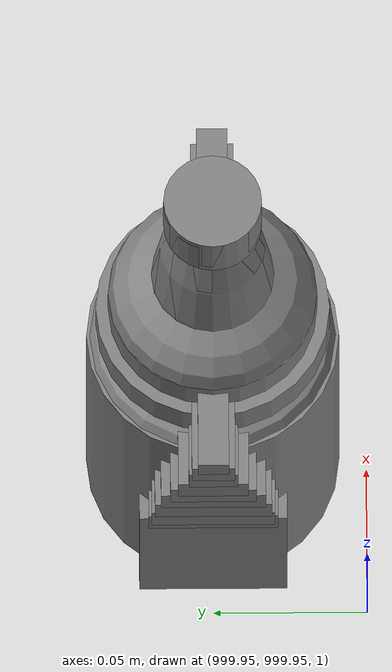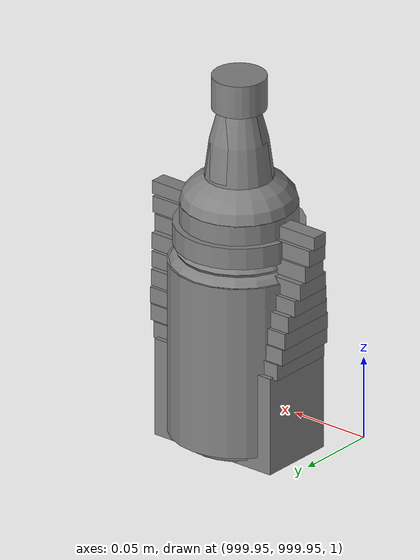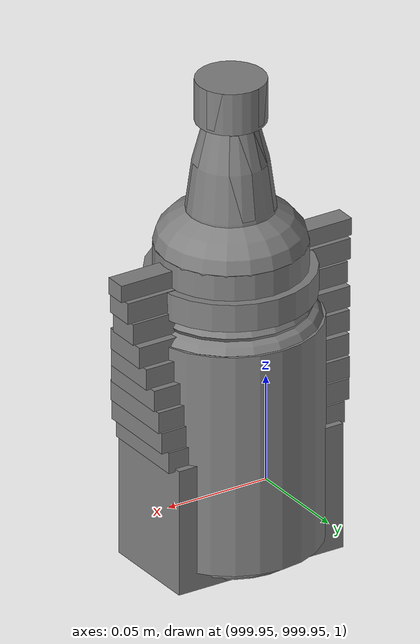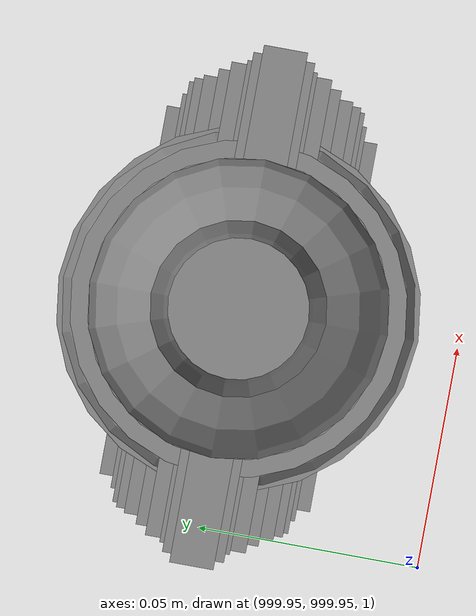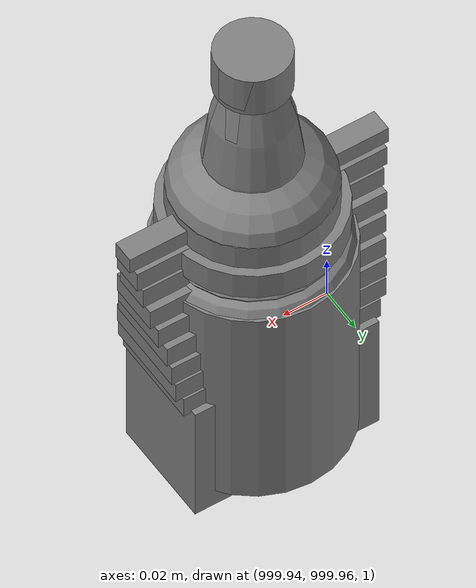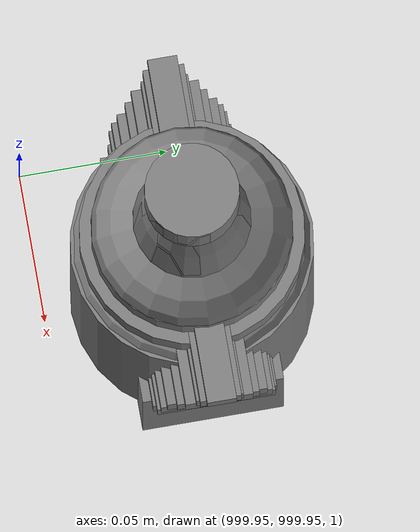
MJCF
<mujoco>
    <option gravity="0.000000000 0.000000000 -9.810000420" timestep="0.0166666" integrator="implicitfast" density="1.225" viscosity="1.8000001e-05" noslip_iterations="10" iterations="100" sdf_iterations="50">
        <flag multiccd="disable"/>
    </option>
    <size memory="1000M"/>
    <compiler coordinate="local"/>
    <worldbody>
        <light cutoff="30" pos="0 1 1" dir="0 -1 -2"/>
        <light cutoff="30" pos="0 -1 1" dir="0 1 -2"/>
        <body pos="-7.168000221 2.823999882 1.227496982" euler="-0.283413976 0.056829724 -0.133293271" name="openloong_gripper_2f85_fix_base_usda_Pos">
            <geom contype="1" conaffinity="1" density="1000" type="box" material="" rgba="0.500000000 0.500000000 0.500000000 1.000000000" solimp="0.899999976 0.949999988 0.001000000" friction="1.000000000 0.005000000 0.000100000" solref="0.020000000 1.000000000" margin="0" condim="3" group="0" pos="-0.002278805 0.074524641 -0.004134059" quat="0.315989345 0.948763072 -0.000000000 0.000000000" size="0.059999999 0.013000000 0.035000000" name="openloong_gripper_2f85_fix_base_usda_geom_DF3D19B0_8293_4397_82CA_4059F74650A2"/>
            <geom contype="1" conaffinity="1" density="1000" type="box" material="" rgba="0.500000000 0.500000000 0.500000000 1.000000000" solimp="0.899999976 0.949999988 0.001000000" friction="1.000000000 0.005000000 0.000100000" solref="0.020000000 1.000000000" margin="0" condim="3" group="0" pos="-0.002278805 0.078031301 0.008128285" quat="0.990447521 -0.137893379 -0.000000000 -0.000000000" size="0.059999999 0.010000000 0.035000000" name="openloong_gripper_2f85_fix_base_usda_geom_9A256A86_27F9_47F3_BDA7_986834A74CBF"/>
            <geom contype="1" conaffinity="1" density="1000" type="box" material="" rgba="0.500000000 0.500000000 0.500000000 1.000000000" solimp="0.899999976 0.949999988 0.001000000" friction="1.000000000 0.005000000 0.000100000" solref="0.020000000 1.000000000" margin="0" condim="3" group="0" pos="-0.002278805 0.080785275 -0.002596974" quat="0.287325472 -0.957833409 0.000000000 -0.000000000" size="0.059999999 0.013000000 0.035000000" name="openloong_gripper_2f85_fix_base_usda_geom_B77707F9_179E_47C5_A2D7_D2B25FC6F83A"/>
            <geom contype="1" conaffinity="1" density="1000" type="box" material="" rgba="0.500000000 0.500000000 0.500000000 1.000000000" solimp="0.899999976 0.949999988 0.001000000" friction="1.000000000 0.005000000 0.000100000" solref="0.020000000 1.000000000" margin="0" condim="3" group="0" pos="-0.002278805 -0.098804474 -0.020146966" quat="0.988851666 0.148906454 0.000000000 -0.000000000" size="0.059999999 0.022000000 0.020000000" name="openloong_gripper_2f85_fix_base_usda_geom_C3900E1C_CC1F_4574_9CBB_27F60CF69C2C"/>
            <geom contype="1" conaffinity="1" density="1000" type="box" material="" rgba="0.500000000 0.500000000 0.500000000 1.000000000" solimp="0.899999976 0.949999988 0.001000000" friction="1.000000000 0.005000000 0.000100000" solref="0.020000000 1.000000000" margin="0" condim="3" group="0" pos="-0.002279282 0.019920111 0.012102962" quat="0.995421767 0.095583342 -0.000000000 -0.000000000" size="0.059999999 0.025000000 0.026000001" name="openloong_gripper_2f85_fix_base_usda_geom_325F870E_E3B8_45D0_832D_AC0EE87419BB"/>
            <geom contype="1" conaffinity="1" density="1000" type="box" material="" rgba="0.500000000 0.500000000 0.500000000 1.000000000" solimp="0.899999976 0.949999988 0.001000000" friction="1.000000000 0.005000000 0.000100000" solref="0.020000000 1.000000000" margin="0" condim="3" group="0" pos="-0.002279282 0.005734444 -0.014276862" quat="0.999571741 -0.029275302 -0.000000000 -0.000000000" size="0.059999999 0.050000001 0.010000000" name="openloong_gripper_2f85_fix_base_usda_geom_063535C5_A522_47E0_9906_6981B1CDBE03"/>
            <geom contype="1" conaffinity="1" density="1000" type="box" material="" rgba="0.500000000 0.500000000 0.500000000 1.000000000" solimp="0.899999976 0.949999988 0.001000000" friction="1.000000000 0.005000000 0.000100000" solref="0.020000000 1.000000000" margin="0" condim="3" group="0" pos="-0.002278805 0.079460382 0.007771969" quat="0.922590554 -0.385781586 0.000000000 -0.000000000" size="0.059999999 0.010000000 0.035000000" name="openloong_gripper_2f85_fix_base_usda_geom_CF62DDBD_7768_409B_B7A9_467BD8379B39"/>
            <geom contype="1" conaffinity="1" density="1000" type="box" material="" rgba="0.500000000 0.500000000 0.500000000 1.000000000" solimp="0.899999976 0.949999988 0.001000000" friction="1.000000000 0.005000000 0.000100000" solref="0.020000000 1.000000000" margin="0" condim="3" group="0" pos="-0.002279282 0.081384182 -0.001320124" quat="0.590483785 -0.807049930 0.000000000 -0.000000000" size="0.059999999 0.013000000 0.035000000" name="openloong_gripper_2f85_fix_base_usda_geom_A6E511AF_1AA5_4547_B51F_896EDDB28E65"/>
            <geom contype="1" conaffinity="1" density="1000" type="box" material="" rgba="0.500000000 0.500000000 0.500000000 1.000000000" solimp="0.899999976 0.949999988 0.001000000" friction="1.000000000 0.005000000 0.000100000" solref="0.020000000 1.000000000" margin="0" condim="3" group="0" pos="-0.002278805 -0.059297800 -0.007972836" quat="0.988851666 0.148906454 0.000000000 -0.000000000" size="0.059999999 0.020000000 0.022000000" name="openloong_gripper_2f85_fix_base_usda_geom_03D7FD25_621A_4D7E_A366_01D92EA2EDB2"/>
            <geom contype="1" conaffinity="1" density="1000" type="box" material="" rgba="0.500000000 0.500000000 0.500000000 1.000000000" solimp="0.899999976 0.949999988 0.001000000" friction="1.000000000 0.005000000 0.000100000" solref="0.020000000 1.000000000" margin="0" condim="3" group="0" pos="-0.002278805 0.076618671 -0.004656792" quat="0.004634961 0.999989629 -0.000000000 0.000000000" size="0.059999999 0.013000000 0.035000000" name="openloong_gripper_2f85_fix_base_usda_geom_0CEF3A63_695E_4864_A86E_D43F8C3377CB"/>
            <geom contype="1" conaffinity="1" density="1000" type="box" material="" rgba="0.500000000 0.500000000 0.500000000 1.000000000" solimp="0.899999976 0.949999988 0.001000000" friction="1.000000000 0.005000000 0.000100000" solref="0.020000000 1.000000000" margin="0" condim="3" group="0" pos="-0.002279282 -0.021952629 0.002960086" quat="0.991270423 0.131847665 -0.000000000 0.000000000" size="0.059999999 0.020000000 0.024000000" name="openloong_gripper_2f85_fix_base_usda_geom_8038A967_89AC_43C8_8B74_9F4253981462"/>
            <geom contype="1" conaffinity="1" density="1000" type="box" material="" rgba="0.500000000 0.500000000 0.500000000 1.000000000" solimp="0.899999976 0.949999988 0.001000000" friction="1.000000000 0.005000000 0.000100000" solref="0.020000000 1.000000000" margin="0" condim="3" group="0" pos="-0.002278805 0.081418991 0.002587914" quat="0.803492308 -0.595315695 0.000000000 -0.000000000" size="0.059999999 0.013000000 0.035000000" name="openloong_gripper_2f85_fix_base_usda_geom_3356CB52_13BD_420C_9215_F78C1E453AC5"/>
            <geom contype="1" conaffinity="1" density="1000" type="box" material="" rgba="0.500000000 0.500000000 0.500000000 1.000000000" solimp="0.899999976 0.949999988 0.001000000" friction="1.000000000 0.005000000 0.000100000" solref="0.020000000 1.000000000" margin="0" condim="3" group="0" pos="-0.002278805 0.061115503 0.008545756" quat="0.999326169 0.036714450 0.000000000 -0.000000000" size="0.059999999 0.020000000 0.035000000" name="openloong_gripper_2f85_fix_base_usda_geom_31D5F521_9817_4838_8321_565E1971BC55"/>
            <freejoint name="openloong_gripper_2f85_fix_base_usda_pos_scan"/>
        </body>
        <body pos="-2.246339560 6.530765057 1.793992758" euler="179.974853516 44.430862427 -124.821342468" mocap="true" name="spotlight5_SpotLight"/>
        <body pos="-2.290434361 6.572346210 1.739992380" euler="40.863040924 49.905731201 78.971374512" mocap="true" name="spotlight2_SpotLight"/>
        <body pos="-1.899507403 6.095312595 1.859030128" euler="-136.790878296 29.303886414 -108.591728210" mocap="true" name="spotlight4_SpotLight"/>
        <body pos="1000.000000000 1000.000000000 1.000000000" euler="0.000000000 0.000000000 0.000000000" name="openloong_gripper_2f85_fix_base_usda_salt">
            <geom contype="1" conaffinity="1" density="1000" type="box" material="" rgba="0.500000000 0.500000000 0.500000000 1.000000000" solimp="0.899999976 0.949999988 0.001000000" friction="1.000000000 0.005000000 0.000100000" solref="0.020000000 1.000000000" margin="0" condim="3" group="0" pos="0.000305176 0.000000000 0.084862232" quat="1.000000000 0.000000000 0.000000000 0.000000000" size="0.048999999 0.018999999 0.005000000" name="openloong_gripper_2f85_fix_base_usda_geom_1849E151_6100_4AC5_807C_8881F1C19A57"/>
            <geom contype="1" conaffinity="1" density="1000" type="box" material="" rgba="0.500000000 0.500000000 0.500000000 1.000000000" solimp="0.899999976 0.949999988 0.001000000" friction="1.000000000 0.005000000 0.000100000" solref="0.020000000 1.000000000" margin="0" condim="3" group="0" pos="0.000305176 0.000000000 0.104564309" quat="1.000000000 0.000000000 0.000000000 0.000000000" size="0.052000001 0.014000000 0.005000000" name="openloong_gripper_2f85_fix_base_usda_geom_814A06C3_173B_4D83_8835_5A55BF47DD52"/>
            <geom contype="1" conaffinity="1" density="1000" type="box" material="" rgba="0.500000000 0.500000000 0.500000000 1.000000000" solimp="0.899999976 0.949999988 0.001000000" friction="1.000000000 0.005000000 0.000100000" solref="0.020000000 1.000000000" margin="0" condim="3" group="0" pos="0.000305176 0.000000000 0.114487171" quat="1.000000000 0.000000000 0.000000000 0.000000000" size="0.054000001 0.011500000 0.005000000" name="openloong_gripper_2f85_fix_base_usda_geom_33916695_9440_45FE_960E_5AA6A4408608"/>
            <geom contype="1" conaffinity="1" density="1000" type="box" material="" rgba="0.500000000 0.500000000 0.500000000 1.000000000" solimp="0.899999976 0.949999988 0.001000000" friction="1.000000000 0.005000000 0.000100000" solref="0.020000000 1.000000000" margin="0" condim="3" group="0" pos="0.000305176 0.000000000 0.075103164" quat="1.000000000 0.000000000 0.000000000 0.000000000" size="0.048000000 0.020000000 0.005000000" name="openloong_gripper_2f85_fix_base_usda_geom_088AEF5B_D282_4975_8761_19AA9ED86B0F"/>
            <geom contype="1" conaffinity="1" density="1000" type="box" material="" rgba="0.500000000 0.500000000 0.500000000 1.000000000" solimp="0.899999976 0.949999988 0.001000000" friction="1.000000000 0.005000000 0.000100000" solref="0.020000000 1.000000000" margin="0" condim="3" group="0" pos="0.000305176 0.000000000 0.134892464" quat="1.000000000 0.000000000 0.000000000 0.000000000" size="0.057000000 0.007000000 0.005000000" name="openloong_gripper_2f85_fix_base_usda_geom_9FAED394_BC17_4F22_A265_F91BF3A09F02"/>
            <geom contype="1" conaffinity="1" density="1000" type="box" material="" rgba="0.500000000 0.500000000 0.500000000 1.000000000" solimp="0.899999976 0.949999988 0.001000000" friction="1.000000000 0.005000000 0.000100000" solref="0.020000000 1.000000000" margin="0" condim="3" group="0" pos="0.000305176 0.000000000 0.094920278" quat="1.000000000 0.000000000 0.000000000 0.000000000" size="0.050000001 0.017000001 0.005000000" name="openloong_gripper_2f85_fix_base_usda_geom_035CCD63_B43F_4F31_9CF3_C15B066E173D"/>
            <geom contype="1" conaffinity="1" density="1000" type="box" material="" rgba="0.500000000 0.500000000 0.500000000 1.000000000" solimp="0.899999976 0.949999988 0.001000000" friction="1.000000000 0.005000000 0.000100000" solref="0.020000000 1.000000000" margin="0" condim="3" group="0" pos="0.000305176 0.000000000 0.065204859" quat="1.000000000 0.000000000 0.000000000 0.000000000" size="0.045000002 0.021000000 0.005000000" name="openloong_gripper_2f85_fix_base_usda_geom_7C10485A_B886_4DB7_A914_8030F65AF658"/>
            <geom contype="1" conaffinity="1" density="1000" type="box" material="" rgba="0.500000000 0.500000000 0.500000000 1.000000000" solimp="0.899999976 0.949999988 0.001000000" friction="1.000000000 0.005000000 0.000100000" solref="0.020000000 1.000000000" margin="0" condim="3" group="0" pos="0.000305176 0.000000000 0.144135714" quat="1.000000000 0.000000000 0.000000000 0.000000000" size="0.059000000 0.005000000 0.004000000" name="openloong_gripper_2f85_fix_base_usda_geom_7E26E0C7_4C32_4892_B5C3_98DC5C7D03D1"/>
            <geom contype="1" conaffinity="1" density="1000" type="box" material="" rgba="0.500000000 0.500000000 0.500000000 1.000000000" solimp="0.899999976 0.949999988 0.001000000" friction="1.000000000 0.005000000 0.000100000" solref="0.020000000 1.000000000" margin="0" condim="3" group="0" pos="0.000000000 0.000000000 0.031593561" quat="1.000000000 0.000000000 0.000000000 0.000000000" size="0.041999999 0.024000000 0.029999999" name="openloong_gripper_2f85_fix_base_usda_geom_0FF7427F_7DE5_4152_9994_8BE988934041"/>
            <geom contype="1" conaffinity="1" density="1000" type="box" material="" rgba="0.500000000 0.500000000 0.500000000 1.000000000" solimp="0.899999976 0.949999988 0.001000000" friction="1.000000000 0.005000000 0.000100000" solref="0.020000000 1.000000000" margin="0" condim="3" group="0" pos="0.000305176 0.000000000 0.124608755" quat="1.000000000 0.000000000 0.000000000 0.000000000" size="0.055000000 0.008000000 0.005000000" name="openloong_gripper_2f85_fix_base_usda_geom_8AA06108_F885_4013_8CF8_9FB31D741E70"/>
            <freejoint name="openloong_gripper_2f85_fix_base_usda_salt_joint"/>
            <site size="0.005000000 0.005000000 0.005000000" rgba="0.500000000 0.500000000 0.500000000 1.000000000" pos="0.000000000 0.000000000 0.000000000" quat="1.000000000 0.000000000 0.000000000 0.000000000" group="0" type="sphere" name="openloong_gripper_2f85_fix_base_usda_saltsite"/>
        </body>
        <body pos="1000.000000000 1000.000000000 1.000000000" euler="0.000000000 0.000000000 0.000000000" name="openloong_gripper_2f85_fix_base_usda_bottle_blue">
            <geom contype="1" conaffinity="1" density="1000" type="ellipsoid" material="" rgba="0.500000000 0.500000000 0.500000000 1.000000000" solimp="0.899999976 0.949999988 0.001000000" friction="1.000000000 0.005000000 0.000100000" solref="0.020000000 1.000000000" margin="0" condim="3" group="0" pos="0.000000000 0.000000000 0.118920922" quat="1.000000000 0.000000000 0.000000000 0.000000000" size="0.030999999 0.030999999 0.029999999" name="openloong_gripper_2f85_fix_base_usda_geom_45EE85C2_3F14_43BC_9B7A_F392D3AC2745"/>
            <geom contype="1" conaffinity="1" density="1000" type="box" material="" rgba="0.500000000 0.500000000 0.500000000 1.000000000" solimp="0.899999976 0.949999988 0.001000000" friction="1.000000000 0.005000000 0.000100000" solref="0.020000000 1.000000000" margin="0" condim="3" group="0" pos="0.000000000 0.000000000 0.002164602" quat="1.000000000 0.000000000 0.000000000 0.000000000" size="0.020000000 0.020000000 0.003000000" name="openloong_gripper_2f85_fix_base_usda_geom_9AEEFBC4_65D9_4695_AE37_286B2B78835E"/>
            <geom contype="1" conaffinity="1" density="1000" type="cylinder" material="" rgba="0.500000000 0.500000000 0.500000000 1.000000000" solimp="0.899999976 0.949999988 0.001000000" friction="1.000000000 0.005000000 0.000100000" solref="0.020000000 1.000000000" margin="0" condim="3" group="0" pos="0.000000000 -0.000366211 0.060859680" quat="1.000000000 0.000000000 0.000000000 0.000000000" size="0.030999999 0.057999998 1.000000000" name="openloong_gripper_2f85_fix_base_usda_geom_45981436_C301_4C58_8AE5_FB29C14FCB20"/>
            <geom contype="1" conaffinity="1" density="1000" type="cylinder" material="" rgba="0.500000000 0.500000000 0.500000000 1.000000000" solimp="0.899999976 0.949999988 0.001000000" friction="1.000000000 0.005000000 0.000100000" solref="0.020000000 1.000000000" margin="0" condim="3" group="0" pos="0.000000000 0.000000000 0.220594406" quat="1.000000000 0.000000000 0.000000000 0.000000000" size="0.016000001 0.010000000 1.000000000" name="openloong_gripper_2f85_fix_base_usda_geom_CD04C6DD_9F37_41EE_8530_45B1B25C4D25"/>
            <geom contype="1" conaffinity="1" density="1000" type="ellipsoid" material="" rgba="0.500000000 0.500000000 0.500000000 1.000000000" solimp="0.899999976 0.949999988 0.001000000" friction="1.000000000 0.005000000 0.000100000" solref="0.020000000 1.000000000" margin="0" condim="3" group="0" pos="0.000000000 0.000000000 0.144259930" quat="1.000000000 0.000000000 0.000000000 0.000000000" size="0.021000000 0.021000000 0.079999998" name="openloong_gripper_2f85_fix_base_usda_geom_86BB7147_522B_4CBC_A90C_4182901B224F"/>
            <freejoint name="openloong_gripper_2f85_fix_base_usda_bottle_blue_joint"/>
            <site size="0.005000000 0.005000000 0.005000000" rgba="0.500000000 0.500000000 0.500000000 1.000000000" pos="0.000000000 0.000000000 0.000000000" quat="0.999961913 0.008726535 0.000000000 0.000000000" group="0" type="sphere" name="openloong_gripper_2f85_fix_base_usda_bottle_bluesite"/>
        </body>
        <body pos="1000.000000000 1000.000000000 1.000000000" euler="0.000000000 0.000000000 0.000000000" name="openloong_gripper_2f85_fix_base_usda_can">
            <geom contype="1" conaffinity="1" density="1000" type="cylinder" material="" rgba="0.500000000 0.500000000 0.500000000 1.000000000" solimp="0.899999976 0.949999988 0.001000000" friction="1.000000000 0.005000000 0.000100000" solref="0.020000000 1.000000000" margin="0" condim="3" group="0" pos="0.000000000 0.000000000 0.079676986" quat="1.000000000 0.000000000 0.000000000 0.000000000" size="0.034000002 0.071999997 1.000000000" name="openloong_gripper_2f85_fix_base_usda_geom_C1ABB6CA_CEEE_4BDA_A317_4D42142782D5"/>
            <geom contype="1" conaffinity="1" density="1000" type="ellipsoid" material="" rgba="0.500000000 0.500000000 0.500000000 1.000000000" solimp="0.899999976 0.949999988 0.001000000" friction="1.000000000 0.005000000 0.000100000" solref="0.020000000 1.000000000" margin="0" condim="3" group="0" pos="0.000000000 0.000000000 0.151854277" quat="1.000000000 0.000000000 0.000000000 0.000000000" size="0.034000002 0.034000002 0.020000000" name="openloong_gripper_2f85_fix_base_usda_geom_12088F14_2E52_4157_B43A_1C6FA00736E6"/>
            <geom contype="1" conaffinity="1" density="1000" type="box" material="" rgba="0.500000000 0.500000000 0.500000000 1.000000000" solimp="0.899999976 0.949999988 0.001000000" friction="1.000000000 0.005000000 0.000100000" solref="0.020000000 1.000000000" margin="0" condim="3" group="0" pos="0.000000000 0.000000000 0.004777670" quat="1.000000000 0.000000000 0.000000000 0.000000000" size="0.020000000 0.020000000 0.005000000" name="openloong_gripper_2f85_fix_base_usda_geom_6A647CD4_FD34_4809_8747_4BC93632092B"/>
            <freejoint name="openloong_gripper_2f85_fix_base_usda_can_joint"/>
            <site size="0.005000000 0.005000000 0.005000000" rgba="0.500000000 0.500000000 0.500000000 1.000000000" pos="0.000000000 0.000000000 0.000000000" quat="1.000000000 0.000000000 0.000000000 0.000000000" group="0" type="sphere" name="openloong_gripper_2f85_fix_base_usda_cansite"/>
        </body>
        <body pos="1000.000000000 1000.000000000 1.000000000" euler="0.000000000 0.000000000 0.000000000" name="openloong_gripper_2f85_fix_base_usda_bottle_red">
            <geom contype="1" conaffinity="1" density="1000" type="ellipsoid" material="" rgba="0.500000000 0.500000000 0.500000000 1.000000000" solimp="0.899999976 0.949999988 0.001000000" friction="1.000000000 0.005000000 0.000100000" solref="0.020000000 1.000000000" margin="0" condim="3" group="0" pos="0.000000000 0.000000000 0.144284487" quat="1.000000000 0.000000000 0.000000000 0.000000000" size="0.021000000 0.021000000 0.079999998" name="openloong_gripper_2f85_fix_base_usda_geom_82A5BA47_2295_48FF_9E06_DDAA8869943A"/>
            <geom contype="1" conaffinity="1" density="1000" type="cylinder" material="" rgba="0.500000000 0.500000000 0.500000000 1.000000000" solimp="0.899999976 0.949999988 0.001000000" friction="1.000000000 0.005000000 0.000100000" solref="0.020000000 1.000000000" margin="0" condim="3" group="0" pos="0.000000000 0.000000000 0.220618963" quat="1.000000000 0.000000000 0.000000000 0.000000000" size="0.016000001 0.010000000 1.000000000" name="openloong_gripper_2f85_fix_base_usda_geom_ED28C9F3_5949_4B74_B554_58F285E0B079"/>
            <geom contype="1" conaffinity="1" density="1000" type="ellipsoid" material="" rgba="0.500000000 0.500000000 0.500000000 1.000000000" solimp="0.899999976 0.949999988 0.001000000" friction="1.000000000 0.005000000 0.000100000" solref="0.020000000 1.000000000" margin="0" condim="3" group="0" pos="0.000000000 0.000000000 0.118945479" quat="1.000000000 0.000000000 0.000000000 0.000000000" size="0.030999999 0.030999999 0.029999999" name="openloong_gripper_2f85_fix_base_usda_geom_E3E6BC60_831C_4CDF_80F5_AB43D79B8197"/>
            <geom contype="1" conaffinity="1" density="1000" type="box" material="" rgba="0.500000000 0.500000000 0.500000000 1.000000000" solimp="0.899999976 0.949999988 0.001000000" friction="1.000000000 0.005000000 0.000100000" solref="0.020000000 1.000000000" margin="0" condim="3" group="0" pos="0.000000000 0.000000000 0.002189159" quat="1.000000000 0.000000000 0.000000000 0.000000000" size="0.020000000 0.020000000 0.003000000" name="openloong_gripper_2f85_fix_base_usda_geom_D110BB8D_3011_42FD_B75B_9179C60427C6"/>
            <geom contype="1" conaffinity="1" density="1000" type="cylinder" material="" rgba="0.500000000 0.500000000 0.500000000 1.000000000" solimp="0.899999976 0.949999988 0.001000000" friction="1.000000000 0.005000000 0.000100000" solref="0.020000000 1.000000000" margin="0" condim="3" group="0" pos="0.000000000 -0.000366211 0.060884237" quat="1.000000000 0.000000000 0.000000000 0.000000000" size="0.030999999 0.057999998 1.000000000" name="openloong_gripper_2f85_fix_base_usda_geom_F1B3258E_1A65_453B_A86B_28DFC92720C4"/>
            <freejoint name="openloong_gripper_2f85_fix_base_usda_bottle_red_joint"/>
            <site size="0.005000000 0.005000000 0.005000000" rgba="0.500000000 0.500000000 0.500000000 1.000000000" pos="0.000000000 0.000000000 0.000000000" quat="0.999961913 0.008726535 0.000000000 0.000000000" group="0" type="sphere" name="openloong_gripper_2f85_fix_base_usda_bottle_redsite"/>
        </body>
        <body pos="1000.000000000 1000.000000000 1.000000000" euler="0.000000000 0.000000000 0.000000000" name="openloong_gripper_2f85_fix_base_usda_jar_01">
            <geom contype="1" conaffinity="1" density="1000" type="box" material="" rgba="0.500000000 0.500000000 0.500000000 1.000000000" solimp="0.899999976 0.949999988 0.001000000" friction="1.000000000 0.005000000 0.000100000" solref="0.020000000 1.000000000" margin="0" condim="3" group="0" pos="0.000000000 0.000000000 0.006158113" quat="1.000000000 0.000000000 0.000000000 0.000000000" size="0.020000000 0.020000000 0.005000000" name="openloong_gripper_2f85_fix_base_usda_geom_9BA7EACF_11D9_4A46_ACDB_320E10AC28E6"/>
            <geom contype="1" conaffinity="1" density="1000" type="cylinder" material="" rgba="0.500000000 0.500000000 0.500000000 1.000000000" solimp="0.899999976 0.949999988 0.001000000" friction="1.000000000 0.005000000 0.000100000" solref="0.020000000 1.000000000" margin="0" condim="3" group="0" pos="0.000000000 0.000000000 0.062744498" quat="1.000000000 0.000000000 0.000000000 0.000000000" size="0.041000001 0.052999999 1.000000000" name="openloong_gripper_2f85_fix_base_usda_geom_3EEED54B_DA13_4A9F_BFFE_6B484AA44483"/>
            <geom contype="1" conaffinity="1" density="1000" type="ellipsoid" material="" rgba="0.500000000 0.500000000 0.500000000 1.000000000" solimp="0.899999976 0.949999988 0.001000000" friction="1.000000000 0.005000000 0.000100000" solref="0.020000000 1.000000000" margin="0" condim="3" group="0" pos="0.000000000 0.000000000 0.122252703" quat="1.000000000 0.000000000 0.000000000 0.000000000" size="0.035999998 0.035999998 0.010000000" name="openloong_gripper_2f85_fix_base_usda_geom_EE6C637C_C539_44D0_A4A7_C426DDB8392D"/>
            <geom contype="1" conaffinity="1" density="1000" type="cylinder" material="" rgba="0.500000000 0.500000000 0.500000000 1.000000000" solimp="0.899999976 0.949999988 0.001000000" friction="1.000000000 0.005000000 0.000100000" solref="0.020000000 1.000000000" margin="0" condim="3" group="0" pos="0.000000000 0.000000000 0.015747190" quat="1.000000000 0.000000000 0.000000000 0.000000000" size="0.035000000 0.010000000 1.000000000" name="openloong_gripper_2f85_fix_base_usda_geom_84C150DD_6EDA_46B5_8A31_38FAAD8B8A83"/>
            <geom contype="1" conaffinity="1" density="1000" type="ellipsoid" material="" rgba="0.500000000 0.500000000 0.500000000 1.000000000" solimp="0.899999976 0.949999988 0.001000000" friction="1.000000000 0.005000000 0.000100000" solref="0.020000000 1.000000000" margin="0" condim="3" group="0" pos="0.000000000 0.000000000 0.115815401" quat="1.000000000 0.000000000 0.000000000 0.000000000" size="0.039999999 0.039999999 0.010000000" name="openloong_gripper_2f85_fix_base_usda_geom_7722F941_5E1D_4EFE_A3AC_C7FB4D758DF3"/>
            <geom contype="1" conaffinity="1" density="1000" type="cylinder" material="" rgba="0.500000000 0.500000000 0.500000000 1.000000000" solimp="0.899999976 0.949999988 0.001000000" friction="1.000000000 0.005000000 0.000100000" solref="0.020000000 1.000000000" margin="0" condim="3" group="0" pos="0.000000000 0.000000000 0.133183479" quat="1.000000000 0.000000000 0.000000000 0.000000000" size="0.037999999 0.006500000 1.000000000" name="openloong_gripper_2f85_fix_base_usda_geom_F7555582_CBA9_46FB_92AE_226E115C69BF"/>
            <freejoint name="openloong_gripper_2f85_fix_base_usda_jar_01_joint"/>
            <site size="0.005000000 0.005000000 0.005000000" rgba="0.500000000 0.500000000 0.500000000 1.000000000" pos="0.000000000 0.000000000 0.000000000" quat="1.000000000 0.000000000 0.000000000 0.000000000" group="0" type="sphere" name="openloong_gripper_2f85_fix_base_usda_jar_01site"/>
        </body>
        <body pos="0.000000000 0.000000000 0.000000000" euler="0.000000000 0.000000000 0.000000000" name="Interactive Objects_Interactive Objects"/>
        <body pos="0.000000000 0.000000000 0.000000000" euler="0.000000000 0.000000000 0.000000000" name=" Static Objects_ Static Objects">
            <geom contype="1" conaffinity="1" density="1000" type="box" material="" rgba="0.500000000 0.500000000 0.500000000 1.000000000" solimp="0.899999976 0.949999988 0.001000000" friction="1.000000000 0.005000000 0.000100000" solref="0.020000000 1.000000000" margin="0" condim="3" group="0" pos="-6.286010742 6.153595448 1.563861728" quat="0.707107067 0.000000000 0.000000000 0.707106471" size="0.529999971 3.134999990 0.025000000" name=" Static Objects_geom_CDA1704A_1123_4B06_A9E4_AAB33E055F31"/>
            <geom contype="1" conaffinity="1" density="1000" type="box" material="" rgba="0.500000000 0.500000000 0.500000000 1.000000000" solimp="0.899999976 0.949999988 0.001000000" friction="1.000000000 0.005000000 0.000100000" solref="0.020000000 1.000000000" margin="0" condim="3" group="0" pos="-3.101639986 6.150595188 1.018643856" quat="1.000000000 0.000000000 0.000000000 0.000000000" size="0.050000001 0.579999983 1.019999981" name=" Static Objects_geom_AF17B589_1999_4A94_B62C_A42F963633A0"/>
            <geom contype="1" conaffinity="1" density="1000" type="box" material="" rgba="0.500000000 0.500000000 0.500000000 1.000000000" solimp="0.899999976 0.949999988 0.001000000" friction="1.000000000 0.005000000 0.000100000" solref="0.020000000 1.000000000" margin="0" condim="3" group="0" pos="-2.825197220 6.153595448 1.563861728" quat="0.707107067 0.000000000 0.000000000 0.707106471" size="0.550000012 0.239999995 0.025000000" name=" Static Objects_geom_15A95E9D_DE49_48EC_8F01_192E633B90F5"/>
            <geom contype="1" conaffinity="1" density="1000" type="box" material="" rgba="0.500000000 0.500000000 0.500000000 1.000000000" solimp="0.899999976 0.949999988 0.001000000" friction="1.000000000 0.005000000 0.000100000" solref="0.020000000 1.000000000" margin="0" condim="3" group="0" pos="-6.311686516 6.153595448 1.018643856" quat="0.707107067 0.000000000 0.000000000 0.707106471" size="0.050000001 3.150000095 1.019999981" name=" Static Objects_geom_D8A144F7_6227_46D2_A24E_47461629DC87"/>
            <geom contype="1" conaffinity="1" density="1000" type="box" material="" rgba="0.500000000 0.500000000 0.500000000 1.000000000" solimp="0.899999976 0.949999988 0.001000000" friction="1.000000000 0.005000000 0.000100000" solref="0.020000000 1.000000000" margin="0" condim="3" group="0" pos="-2.825197220 6.153595448 1.115278244" quat="0.707107067 0.000000000 0.000000000 0.707106471" size="0.550000012 0.239999995 0.025000000" name=" Static Objects_geom_16A5B7A3_C57F_4A2C_A7A2_0F5AFE17EC2D"/>
            <geom contype="1" conaffinity="1" density="1000" type="box" material="" rgba="0.500000000 0.500000000 0.500000000 1.000000000" solimp="0.899999976 0.949999988 0.001000000" friction="1.000000000 0.005000000 0.000100000" solref="0.020000000 1.000000000" margin="0" condim="3" group="0" pos="-6.293097973 6.153595448 1.114443064" quat="0.707107067 0.000000000 0.000000000 0.707106471" size="0.529999971 3.134999990 0.025000000" name=" Static Objects_geom_E49BDD30_7161_46DF_9B64_1C5C69E900BB"/>
            <geom contype="1" conaffinity="1" density="1000" type="box" material="" rgba="0.500000000 0.500000000 0.500000000 1.000000000" solimp="0.899999976 0.949999988 0.001000000" friction="1.000000000 0.005000000 0.000100000" solref="0.020000000 1.000000000" margin="0" condim="3" group="0" pos="-2.825197220 6.153595448 0.629031777" quat="0.707107067 0.000000000 0.000000000 0.707106471" size="0.550000012 0.239999995 0.025000000" name=" Static Objects_geom_75020CA9_580F_4BDE_9227_C5BA9E9D0615"/>
            <geom contype="1" conaffinity="1" density="1000" type="box" material="" rgba="0.500000000 0.500000000 0.500000000 1.000000000" solimp="0.899999976 0.949999988 0.001000000" friction="1.000000000 0.005000000 0.000100000" solref="0.020000000 1.000000000" margin="0" condim="3" group="0" pos="-6.286010742 6.153595448 0.096129179" quat="0.707107067 0.000000000 0.000000000 0.707106471" size="0.529999971 3.134999990 0.098999999" name=" Static Objects_geom_8F0B581C_9746_4115_A379_5075F1CC4BE1"/>
            <geom contype="1" conaffinity="1" density="1000" type="box" material="" rgba="0.500000000 0.500000000 0.500000000 1.000000000" solimp="0.899999976 0.949999988 0.001000000" friction="1.000000000 0.005000000 0.000100000" solref="0.020000000 1.000000000" margin="0" condim="3" group="0" pos="-2.825197220 6.153595448 0.097434282" quat="0.707107067 0.000000000 0.000000000 0.707106471" size="0.550000012 0.239999995 0.098999999" name=" Static Objects_geom_D6717BA3_6DCD_4C52_8711_5FE6EED6EA0F"/>
            <geom contype="1" conaffinity="1" density="1000" type="box" material="" rgba="0.500000000 0.500000000 0.500000000 1.000000000" solimp="0.899999976 0.949999988 0.001000000" friction="1.000000000 0.005000000 0.000100000" solref="0.020000000 1.000000000" margin="0" condim="3" group="0" pos="-6.286010742 6.153595448 0.629031777" quat="0.707107067 0.000000000 0.000000000 0.707106471" size="0.529999971 3.134999990 0.025000000" name=" Static Objects_geom_D8D1DADE_B9FC_46A3_A14E_6B7DCB744113"/>
            <geom contype="1" conaffinity="1" density="1000" type="box" material="" rgba="0.500000000 0.500000000 0.500000000 1.000000000" solimp="0.899999976 0.949999988 0.001000000" friction="1.000000000 0.005000000 0.000100000" solref="0.020000000 1.000000000" margin="0" condim="3" group="0" pos="-6.000000000 20.159999847 2.000000000" quat="1.000000000 0.000000000 0.000000000 0.000000000" size="6.079999924 0.070000000 2.000000000" name=" Static Objects_geom_EFAE3C25_686F_4E5E_BBA6_60F0A073DED9"/>
            <geom contype="1" conaffinity="1" density="1000" type="box" material="" rgba="0.500000000 0.500000000 0.500000000 1.000000000" solimp="0.899999976 0.949999988 0.001000000" friction="1.000000000 0.005000000 0.000100000" solref="0.020000000 1.000000000" margin="0" condim="3" group="0" pos="-6.000000000 0.035000000 2.000000000" quat="1.000000000 0.000000000 0.000000000 0.000000000" size="6.079999924 0.070000000 2.000000000" name=" Static Objects_geom_11943BA6_4A25_451B_8D40_07BBB8E337B9"/>
            <geom contype="1" conaffinity="1" density="1000" type="box" material="" rgba="0.500000000 0.500000000 0.500000000 1.000000000" solimp="0.899999976 0.949999988 0.001000000" friction="1.000000000 0.005000000 0.000100000" solref="0.020000000 1.000000000" margin="0" condim="3" group="0" pos="0.000000000 10.000000000 2.000000000" quat="1.000000000 0.000000000 0.000000000 0.000000000" size="0.070000000 10.500000000 2.000000000" name=" Static Objects_geom_2AF011C5_CA2B_454A_8557_A814BBBF79A2"/>
            <geom contype="1" conaffinity="1" density="1000" type="box" material="" rgba="0.500000000 0.500000000 0.500000000 1.000000000" solimp="0.899999976 0.949999988 0.001000000" friction="1.000000000 0.005000000 0.000100000" solref="0.020000000 1.000000000" margin="0" condim="3" group="0" pos="-12.050000191 10.000000000 2.000000000" quat="1.000000000 0.000000000 0.000000000 0.000000000" size="0.070000000 10.500000000 2.000000000" name=" Static Objects_geom_B79F4AB2_17DE_4D10_B66F_F8D928D9DA59"/>
            <geom contype="1" conaffinity="1" density="1000" type="plane" material="" rgba="0.500000000 0.500000000 0.500000000 1.000000000" solimp="0.899999976 0.949999988 0.001000000" friction="1.000000000 0.005000000 0.000100000" solref="0.020000000 1.000000000" margin="0" condim="3" group="0" pos="-6.000000000 10.399999619 0.000000000" quat="1.000000000 0.000000000 0.000000000 0.000000000" size="6.050000191 10.800000191 0.010000000" name=" Static Objects_geom_1CADB4B1_3236_4E22_A685_BA5165E6B158"/>
            <geom contype="1" conaffinity="1" density="1000" type="box" material="" rgba="0.500000000 0.500000000 0.500000000 1.000000000" solimp="0.899999976 0.949999988 0.001000000" friction="1.000000000 0.005000000 0.000100000" solref="0.020000000 1.000000000" margin="0" condim="3" group="0" pos="-8.830721855 2.096410990 0.549305558" quat="1.000000000 0.000000000 0.000000000 0.000000000" size="0.280000001 0.430000007 0.550000012" name=" Static Objects_geom_5D6606C4_6499_41F2_A7CB_D887CF08A50F"/>
            <geom contype="1" conaffinity="1" density="1000" type="box" material="" rgba="0.500000000 0.500000000 0.500000000 1.000000000" solimp="0.899999976 0.949999988 0.001000000" friction="1.000000000 0.005000000 0.000100000" solref="0.020000000 1.000000000" margin="0" condim="3" group="0" pos="-6.460197449 2.937205315 0.548931718" quat="1.000000000 0.000000000 0.000000000 0.000000000" size="2.650000095 0.430000007 0.550000012" name=" Static Objects_geom_AB9A087D_F606_4FE8_AC92_22B830890DA9"/>
            <geom contype="1" conaffinity="1" density="1000" type="box" material="" rgba="0.500000000 0.500000000 0.500000000 1.000000000" solimp="0.899999976 0.949999988 0.001000000" friction="1.000000000 0.005000000 0.000100000" solref="0.020000000 1.000000000" margin="0" condim="3" group="0" pos="-4.240264893 1.327049494 0.549888909" quat="1.000000000 0.000000000 0.000000000 0.000000000" size="0.430000007 1.200000048 0.550000012" name=" Static Objects_geom_03216D11_FE4C_4F59_8D78_3EC5A18FEF35"/>
            <geom contype="1" conaffinity="1" density="1000" type="box" material="" rgba="0.500000000 0.500000000 0.500000000 1.000000000" solimp="0.899999976 0.949999988 0.001000000" friction="1.000000000 0.005000000 0.000100000" solref="0.020000000 1.000000000" margin="0" condim="3" group="0" pos="-7.408766270 3.088089943 1.776644945" quat="0.928051054 0.000000000 0.000000000 0.372453064" size="0.050000001 0.100000001 0.050000001" name=" Static Objects_geom_7DB79482_D064_44AE_AC55_33925EB99AF0"/>
            <geom contype="1" conaffinity="1" density="1000" type="box" material="" rgba="0.500000000 0.500000000 0.500000000 1.000000000" solimp="0.899999976 0.949999988 0.001000000" friction="1.000000000 0.005000000 0.000100000" solref="0.020000000 1.000000000" margin="0" condim="3" group="0" pos="-7.437745571 3.067511320 1.289965630" quat="1.000000000 0.000000000 0.000000000 0.000000000" size="0.029999999 0.020000000 0.020000000" name=" Static Objects_geom_973F220E_1150_4822_9720_536D8EEEED50"/>
            <geom contype="1" conaffinity="1" density="1000" type="box" material="" rgba="0.500000000 0.500000000 0.500000000 1.000000000" solimp="0.899999976 0.949999988 0.001000000" friction="1.000000000 0.005000000 0.000100000" solref="0.020000000 1.000000000" margin="0" condim="3" group="0" pos="-7.719123363 2.867671013 1.173410416" quat="1.000000000 0.000000000 0.000000000 0.000000000" size="0.250000000 0.250000000 0.079999998" name=" Static Objects_geom_A74C71F6_5169_4269_87B2_9C8E47AFBA70"/>
            <geom contype="1" conaffinity="1" density="1000" type="box" material="" rgba="0.500000000 0.500000000 0.500000000 1.000000000" solimp="0.899999976 0.949999988 0.001000000" friction="1.000000000 0.005000000 0.000100000" solref="0.020000000 1.000000000" margin="0" condim="3" group="0" pos="-7.719123363 2.958004713 1.530241251" quat="1.000000000 0.000000000 0.000000000 0.000000000" size="0.250000000 0.159999996 0.280000001" name=" Static Objects_geom_93182786_993D_4E8B_AC3A_1D7E90B4E9A5"/>
            <geom contype="1" conaffinity="1" density="1000" type="cylinder" material="" rgba="0.500000000 0.500000000 0.500000000 1.000000000" solimp="0.899999976 0.949999988 0.001000000" friction="1.000000000 0.005000000 0.000100000" solref="0.020000000 1.000000000" margin="0" condim="3" group="0" pos="-7.427312374 3.069516420 1.502544641" quat="0.928051054 0.000000000 0.000000000 0.372453064" size="0.015000000 0.230000004 0.100000001" name=" Static Objects_geom_6C4F4472_4044_4350_BF8E_0923223FCD45"/>
            <geom contype="1" conaffinity="1" density="1000" type="box" material="" rgba="0.500000000 0.500000000 0.500000000 1.000000000" solimp="0.899999976 0.949999988 0.001000000" friction="1.000000000 0.005000000 0.000100000" solref="0.020000000 1.000000000" margin="0" condim="3" group="0" pos="-9.058088303 6.434794426 1.209077358" quat="1.000000000 0.000000000 0.000000000 0.000000000" size="0.250000000 0.100000001 0.070000000" name=" Static Objects_geom_52D3F23D_03AF_4AC2_A380_C31ADF4C3C2F"/>
            <geom contype="1" conaffinity="1" density="1000" type="box" material="" rgba="0.500000000 0.500000000 0.500000000 1.000000000" solimp="0.899999976 0.949999988 0.001000000" friction="1.000000000 0.005000000 0.000100000" solref="0.020000000 1.000000000" margin="0" condim="3" group="0" pos="-5.611940861 6.318420410 0.350975692" quat="1.000000000 0.000000000 0.000000000 0.000000000" size="0.699999988 0.100000001 0.150000006" name=" Static Objects_geom_2FDEEEF5_9B04_4CC1_B7FA_8D7DACEDE71D"/>
            <geom contype="1" conaffinity="1" density="1000" type="box" material="" rgba="0.500000000 0.500000000 0.500000000 1.000000000" solimp="0.899999976 0.949999988 0.001000000" friction="1.000000000 0.005000000 0.000100000" solref="0.020000000 1.000000000" margin="0" condim="3" group="0" pos="-9.237723351 6.464855671 1.209077358" quat="1.000000000 0.000000000 0.000000000 0.000000000" size="0.100000001 0.100000001 0.070000000" name=" Static Objects_geom_C930D8DC_58F7_449E_9F59_804E36CA33AB"/>
            <geom contype="1" conaffinity="1" density="1000" type="box" material="" rgba="0.500000000 0.500000000 0.500000000 1.000000000" solimp="0.899999976 0.949999988 0.001000000" friction="1.000000000 0.005000000 0.000100000" solref="0.020000000 1.000000000" margin="0" condim="3" group="0" pos="-6.300771236 6.459744930 1.744376063" quat="1.000000000 0.000000000 0.000000000 0.000000000" size="3.000000000 0.200000003 0.150000006" name=" Static Objects_geom_E7C575E8_D67D_4092_BC79_033EFDCD01E9"/>
            <geom contype="1" conaffinity="1" density="1000" type="box" material="" rgba="0.500000000 0.500000000 0.500000000 1.000000000" solimp="0.899999976 0.949999988 0.001000000" friction="1.000000000 0.005000000 0.000100000" solref="0.020000000 1.000000000" margin="0" condim="3" group="0" pos="-7.373087406 6.458900928 1.214329123" quat="1.000000000 0.000000000 0.000000000 0.000000000" size="0.250000000 0.200000003 0.075000003" name=" Static Objects_geom_F62B93DB_B892_49C6_9A47_112A85452CBC"/>
            <geom contype="1" conaffinity="1" density="1000" type="box" material="" rgba="0.500000000 0.500000000 0.500000000 1.000000000" solimp="0.899999976 0.949999988 0.001000000" friction="1.000000000 0.005000000 0.000100000" solref="0.020000000 1.000000000" margin="0" condim="3" group="0" pos="-4.035642624 6.459744930 0.352518857" quat="1.000000000 0.000000000 0.000000000 0.000000000" size="0.800000012 0.200000003 0.150000006" name=" Static Objects_geom_C2345795_B4E3_4FEB_A277_90BDA51765EB"/>
            <geom contype="1" conaffinity="1" density="1000" type="box" material="" rgba="0.500000000 0.500000000 0.500000000 1.000000000" solimp="0.899999976 0.949999988 0.001000000" friction="1.000000000 0.005000000 0.000100000" solref="0.020000000 1.000000000" margin="0" condim="3" group="0" pos="-3.907610416 6.318625927 0.800981164" quat="1.000000000 0.000000000 0.000000000 0.000000000" size="0.500000000 0.100000001 0.150000006" name=" Static Objects_geom_2B5ED88E_EB61_4C66_A70F_68490020765A"/>
            <geom contype="1" conaffinity="1" density="1000" type="box" material="" rgba="0.500000000 0.500000000 0.500000000 1.000000000" solimp="0.899999976 0.949999988 0.001000000" friction="1.000000000 0.005000000 0.000100000" solref="0.020000000 1.000000000" margin="0" condim="3" group="0" pos="-6.098561764 6.327973843 1.292199373" quat="1.000000000 0.000000000 0.000000000 0.000000000" size="0.500000000 0.100000001 0.150000006" name=" Static Objects_geom_71E3D7DA_26F1_4234_AE2E_2F362924464A"/>
            <geom contype="1" conaffinity="1" density="1000" type="box" material="" rgba="0.500000000 0.500000000 0.500000000 1.000000000" solimp="0.899999976 0.949999988 0.001000000" friction="1.000000000 0.005000000 0.000100000" solref="0.020000000 1.000000000" margin="0" condim="3" group="0" pos="-7.886891365 6.459744930 0.352518857" quat="1.000000000 0.000000000 0.000000000 0.000000000" size="1.500000000 0.200000003 0.150000006" name=" Static Objects_geom_85A28DF6_9658_4F40_BCEC_7EE94D3EA95C"/>
            <geom contype="1" conaffinity="1" density="1000" type="box" material="" rgba="0.500000000 0.500000000 0.500000000 1.000000000" solimp="0.899999976 0.949999988 0.001000000" friction="1.000000000 0.005000000 0.000100000" solref="0.020000000 1.000000000" margin="0" condim="3" group="0" pos="-6.824534416 6.447464466 1.212718010" quat="1.000000000 0.000000000 0.000000000 0.000000000" size="0.100000001 0.100000001 0.075000003" name=" Static Objects_geom_08A7F659_D359_4A56_82B4_5B46E589854C"/>
            <geom contype="1" conaffinity="1" density="1000" type="box" material="" rgba="0.500000000 0.500000000 0.500000000 1.000000000" solimp="0.899999976 0.949999988 0.001000000" friction="1.000000000 0.005000000 0.000100000" solref="0.020000000 1.000000000" margin="0" condim="3" group="0" pos="-4.407354832 6.459744930 1.292199373" quat="1.000000000 0.000000000 0.000000000 0.000000000" size="1.240000010 0.200000003 0.150000006" name=" Static Objects_geom_780026FD_19F2_42A6_A6B2_AAF2EA4040F3"/>
            <geom contype="1" conaffinity="1" density="1000" type="box" material="" rgba="0.500000000 0.500000000 0.500000000 1.000000000" solimp="0.899999976 0.949999988 0.001000000" friction="1.000000000 0.005000000 0.000100000" solref="0.020000000 1.000000000" margin="0" condim="3" group="0" pos="-6.751636982 6.459744930 0.800981164" quat="1.000000000 0.000000000 0.000000000 0.000000000" size="2.200000048 0.200000003 0.150000006" name=" Static Objects_geom_D3907217_D752_4101_BD82_951AD43CDBB8"/>
            <geom contype="1" conaffinity="1" density="1000" type="box" material="" rgba="0.500000000 0.500000000 0.500000000 1.000000000" solimp="0.899999976 0.949999988 0.001000000" friction="1.000000000 0.005000000 0.000100000" solref="0.020000000 1.000000000" margin="0" condim="3" group="0" pos="-6.924745083 6.362090111 1.214329123" quat="1.000000000 0.000000000 0.000000000 0.000000000" size="0.200000003 0.100000001 0.075000003" name=" Static Objects_geom_94554EEE_D7E4_43FE_A56D_3E2BAA175703"/>
            <geom contype="1" conaffinity="1" density="1000" type="box" material="" rgba="0.500000000 0.500000000 0.500000000 1.000000000" solimp="0.899999976 0.949999988 0.001000000" friction="1.000000000 0.005000000 0.000100000" solref="0.020000000 1.000000000" margin="0" condim="3" group="0" pos="-8.844120979 6.464855671 1.209077358" quat="1.000000000 0.000000000 0.000000000 0.000000000" size="0.100000001 0.100000001 0.070000000" name=" Static Objects_geom_E67048F5_16DA_42C8_9FAB_5E7FE37A4022"/>
            <geom contype="1" conaffinity="1" density="1000" type="box" material="" rgba="0.500000000 0.500000000 0.500000000 1.000000000" solimp="0.899999976 0.949999988 0.001000000" friction="1.000000000 0.005000000 0.000100000" solref="0.020000000 1.000000000" margin="0" condim="3" group="0" pos="-3.157672644 6.136868477 1.348373055" quat="1.000000000 0.000000000 0.000000000 0.000000000" size="0.200000003 0.519999981 0.300000012" name=" Static Objects_geom_0478A31C_E20B_4214_A52E_9004B057C64D"/>
        </body>
        <body pos="-6.332345009 2.779978037 1.034067392" euler="0.000000000 0.000000000 0.000000000" name="openloong_gripper_2f85_fix_base_usda_basket">
            <geom contype="1" conaffinity="1" density="100000" type="box" material="" rgba="0.500000000 0.500000000 0.500000000 1.000000000" solimp="0.899999976 0.949999988 0.001000000" friction="1.000000000 0.899999976 0.000100000" solref="0.020000000 1.000000000" margin="0" condim="3" group="0" pos="-0.039724827 -0.188568115 0.167089701" quat="0.997537494 0.070135131 0.000000000 0.000000000" size="0.150000006 0.006000000 0.108000003" name="openloong_gripper_2f85_fix_base_usda_geom_1B0859F4_85C5_4381_90FB_A0F541C57FFD"/>
            <geom contype="1" conaffinity="1" density="100000" type="box" material="" rgba="0.500000000 0.500000000 0.500000000 1.000000000" solimp="0.899999976 0.949999988 0.001000000" friction="1.000000000 0.899999976 0.000100000" solref="0.020000000 1.000000000" margin="0" condim="3" group="0" pos="0.094372749 0.000000000 0.168361664" quat="0.706172049 0.036353335 0.036353379 0.706171215" size="0.200000003 0.006000000 0.108000003" name="openloong_gripper_2f85_fix_base_usda_geom_1892171A_FC35_4BB9_BB24_B8224EA22E3B"/>
            <geom contype="1" conaffinity="1" density="100000" type="box" material="" rgba="0.500000000 0.500000000 0.500000000 1.000000000" solimp="0.899999976 0.949999988 0.001000000" friction="1.000000000 0.899999976 0.000100000" solref="0.020000000 1.000000000" margin="0" condim="3" group="0" pos="-0.039724827 0.000000000 0.068126202" quat="1.000000000 0.000000000 0.000000000 0.000000000" size="0.129999995 0.174999997 0.006000000" name="openloong_gripper_2f85_fix_base_usda_geom_9BB331EA_3E94_4531_99AE_30D40BB5B651"/>
            <geom contype="1" conaffinity="1" density="100000" type="box" material="" rgba="0.500000000 0.500000000 0.500000000 1.000000000" solimp="0.899999976 0.949999988 0.001000000" friction="1.000000000 0.899999976 0.000100000" solref="0.020000000 1.000000000" margin="0" condim="3" group="0" pos="-0.039724827 0.188377380 0.167089701" quat="0.997489929 -0.070808925 0.000000000 0.000000000" size="0.150000006 0.006000000 0.108000003" name="openloong_gripper_2f85_fix_base_usda_geom_B598ED86_1F6E_4C3C_A87B_864C9639C026"/>
            <geom contype="1" conaffinity="1" density="100000" type="box" material="" rgba="0.500000000 0.500000000 0.500000000 1.000000000" solimp="0.899999976 0.949999988 0.001000000" friction="1.000000000 0.899999976 0.000100000" solref="0.020000000 1.000000000" margin="0" condim="3" group="0" pos="-0.172339439 0.000000000 0.168361664" quat="0.706172407 -0.036353018 -0.036353093 0.706170976" size="0.200000003 0.006000000 0.108000003" name="openloong_gripper_2f85_fix_base_usda_geom_1DAB0E6C_5C5A_41B7_BAC9_185144A1FA42"/>
            <freejoint name="openloong_gripper_2f85_fix_base_usda_basket_joint"/>
            <site size="0.005000000 0.005000000 0.005000000" rgba="0.500000000 0.500000000 0.500000000 1.000000000" pos="0.000000000 0.000000000 0.000000000" quat="1.000000000 0.000000000 0.000000000 0.000000000" group="0" type="sphere" name="openloong_gripper_2f85_fix_base_usda_basketsite"/>
        </body>
        <body pos="-3.510578632 3.403555870 -0.000000100" euler="0.000000000 0.000000000 40.200675964" name="openloong_gripper_2f85_fix_base_usda_PZ">
            <geom contype="1" conaffinity="1" density="1000" type="box" material="" rgba="0.500000000 0.500000000 0.500000000 1.000000000" solimp="0.899999976 0.949999988 0.001000000" friction="1.000000000 0.005000000 0.000100000" solref="0.020000000 1.000000000" margin="0" condim="3" group="0" pos="-0.047453165 0.056484699 0.373715430" quat="0.934750080 0.077914521 0.028795123 0.345459938" size="0.180000007 0.010000000 0.379999995" name="openloong_gripper_2f85_fix_base_usda_geom_71551E76_C2C0_4C69_A8DC_0EBE48978930"/>
            <geom contype="1" conaffinity="1" density="1000" type="box" material="" rgba="0.500000000 0.500000000 0.500000000 1.000000000" solimp="0.899999976 0.949999988 0.001000000" friction="1.000000000 0.005000000 0.000100000" solref="0.020000000 1.000000000" margin="0" condim="3" group="0" pos="0.047452450 -0.054376602 0.374072611" quat="0.934387863 -0.082143910 -0.030358355 0.345326364" size="0.180000007 0.010000000 0.379999995" name="openloong_gripper_2f85_fix_base_usda_geom_42FAE10C_9220_4EEE_895A_DE8979788DF2"/>
            <freejoint name="openloong_gripper_2f85_fix_base_usda_PZ"/>
        </body>
        <body pos="-2.436573029 6.404376507 0.137849092" euler="0.000000000 0.000000000 0.000000000" name="openloong_gripper_2f85_fix_base_usda_shoppingtrolley_01">
            <geom contype="1" conaffinity="1" density="1000" type="box" material="" rgba="0.500000000 0.500000000 0.500000000 1.000000000" solimp="0.899999976 0.949999988 0.001000000" friction="1.000000000 0.005000000 0.000100000" solref="0.020000000 1.000000000" margin="0" condim="3" group="0" pos="-0.107458733 0.238907143 0.911498845" quat="0.634576976 0.622505128 -0.330067992 -0.317575932" size="0.017999999 0.022499999 0.035999998" name="openloong_gripper_2f85_fix_base_usda_geom_860441FA_A095_445D_A548_607CE39C8121"/>
            <geom contype="1" conaffinity="1" density="1000" type="box" material="" rgba="0.500000000 0.500000000 0.500000000 1.000000000" solimp="0.899999976 0.949999988 0.001000000" friction="1.000000000 0.005000000 0.000100000" solref="0.020000000 1.000000000" margin="0" condim="3" group="0" pos="-0.126757339 -0.182533979 0.598989725" quat="0.996607184 0.055331606 -0.059003651 -0.015205891" size="0.013499999 0.287999988 0.053999998" name="openloong_gripper_2f85_fix_base_usda_geom_1BD98BBD_10C6_4587_8B1C_3365D67A1063"/>
            <geom contype="1" conaffinity="1" density="1000" type="box" material="" rgba="0.500000000 0.500000000 0.500000000 1.000000000" solimp="0.899999976 0.949999988 0.001000000" friction="1.000000000 0.005000000 0.000100000" solref="0.020000000 1.000000000" margin="0" condim="3" group="0" pos="-0.005004787 0.248085022 0.912686050" quat="1.000000000 0.000000000 0.000000000 0.000000000" size="0.107999995 0.022499999 0.022499999" name="openloong_gripper_2f85_fix_base_usda_geom_EEE0AEC3_F5D9_42D8_8999_C11E23D888C2"/>
            <geom contype="1" conaffinity="1" density="1000" type="box" material="" rgba="0.500000000 0.500000000 0.500000000 1.000000000" solimp="0.899999976 0.949999988 0.001000000" friction="1.000000000 0.005000000 0.000100000" solref="0.020000000 1.000000000" margin="0" condim="3" group="0" pos="-0.169898406 -0.043119621 0.915120542" quat="0.687021017 0.726584017 -0.005590606 -0.006832919" size="0.017999999 0.022499999 0.089999996" name="openloong_gripper_2f85_fix_base_usda_geom_AEF06AD2_F577_4213_A014_E2609A61145D"/>
            <geom contype="1" conaffinity="1" density="1000" type="box" material="" rgba="0.500000000 0.500000000 0.500000000 1.000000000" solimp="0.899999976 0.949999988 0.001000000" friction="1.000000000 0.005000000 0.000100000" solref="0.020000000 1.000000000" margin="0" condim="3" group="0" pos="0.148195267 -0.199506566 0.782808602" quat="0.998808920 0.017156634 0.026950166 0.036880098" size="0.013499999 0.305999994 0.063000001" name="openloong_gripper_2f85_fix_base_usda_geom_8343AB20_9A52_4B74_A47F_6CFD7E87FB0E"/>
            <geom contype="1" conaffinity="1" density="1000" type="box" material="" rgba="0.500000000 0.500000000 0.500000000 1.000000000" solimp="0.899999976 0.949999988 0.001000000" friction="1.000000000 0.005000000 0.000100000" solref="0.020000000 1.000000000" margin="0" condim="3" group="0" pos="-0.142927840 -0.199506134 0.784674108" quat="0.998421252 0.016904408 -0.027109101 -0.046199299" size="0.013499999 0.305999994 0.063000001" name="openloong_gripper_2f85_fix_base_usda_geom_C258EFD6_521A_4C24_813A_497B872BCC77"/>
            <geom contype="1" conaffinity="1" density="1000" type="box" material="" rgba="0.500000000 0.500000000 0.500000000 1.000000000" solimp="0.899999976 0.949999988 0.001000000" friction="1.000000000 0.005000000 0.000100000" solref="0.020000000 1.000000000" margin="0" condim="3" group="0" pos="-0.000004721 -0.174527690 0.560063601" quat="0.996704638 0.081116498 -0.000000004 0.000000000" size="0.126000002 0.287999988 0.009000000" name="openloong_gripper_2f85_fix_base_usda_geom_CA903BF8_7351_4E5C_8B6F_B1AA7E32C029"/>
            <geom contype="1" conaffinity="1" density="1000" type="box" material="" rgba="0.500000000 0.500000000 0.500000000 1.000000000" solimp="0.899999976 0.949999988 0.001000000" friction="1.000000000 0.005000000 0.000100000" solref="0.020000000 1.000000000" margin="0" condim="3" group="0" pos="-0.160832763 0.103427693 0.910528183" quat="0.711469591 0.699786782 -0.048386075 -0.042050660" size="0.017999999 0.022499999 0.071999997" name="openloong_gripper_2f85_fix_base_usda_geom_F033B719_856B_4FF2_9782_E3AB3DECCA0A"/>
            <geom contype="1" conaffinity="1" density="1000" type="box" material="" rgba="0.500000000 0.500000000 0.500000000 1.000000000" solimp="0.899999976 0.949999988 0.001000000" friction="1.000000000 0.005000000 0.000100000" solref="0.020000000 1.000000000" margin="0" condim="3" group="0" pos="-0.169898406 -0.178061336 0.864131629" quat="0.916343808 -0.400392294 -0.000000045 0.000000030" size="0.017999999 0.022499999 0.089999996" name="openloong_gripper_2f85_fix_base_usda_geom_C9359B28_5C5E_44B5_A048_66C24B1F294A"/>
            <geom contype="1" conaffinity="1" density="1000" type="box" material="" rgba="0.500000000 0.500000000 0.500000000 1.000000000" solimp="0.899999976 0.949999988 0.001000000" friction="1.000000000 0.005000000 0.000100000" solref="0.020000000 1.000000000" margin="0" condim="3" group="0" pos="-0.000006008 -0.484932661 0.670727849" quat="0.997585475 0.069449045 -0.000000004 -0.000000089" size="0.179999992 0.013499999 0.170999989" name="openloong_gripper_2f85_fix_base_usda_geom_DC762C6A_4216_446B_A089_39DC72F5D368"/>
            <geom contype="1" conaffinity="1" density="1000" type="box" material="" rgba="0.500000000 0.500000000 0.500000000 1.000000000" solimp="0.899999976 0.949999988 0.001000000" friction="1.000000000 0.005000000 0.000100000" solref="0.020000000 1.000000000" margin="0" condim="3" group="0" pos="0.134013891 0.200098798 0.912192523" quat="0.692574680 -0.680924535 -0.166899428 0.169783980" size="0.017999999 0.022499999 0.035999998" name="openloong_gripper_2f85_fix_base_usda_geom_2D08203C_95D1_4958_85F1_CE6C63F39296"/>
            <geom contype="1" conaffinity="1" density="1000" type="box" material="" rgba="0.500000000 0.500000000 0.500000000 1.000000000" solimp="0.899999976 0.949999988 0.001000000" friction="1.000000000 0.005000000 0.000100000" solref="0.020000000 1.000000000" margin="0" condim="3" group="0" pos="0.141839072 -0.191051379 0.702451229" quat="0.997147262 0.056065105 0.045779929 0.021407485" size="0.013499999 0.287999988 0.053999998" name="openloong_gripper_2f85_fix_base_usda_geom_D3842B69_29E5_4147_8CB7_4F9A7FC4D99C"/>
            <geom contype="1" conaffinity="1" density="1000" type="box" material="" rgba="0.500000000 0.500000000 0.500000000 1.000000000" solimp="0.899999976 0.949999988 0.001000000" friction="1.000000000 0.005000000 0.000100000" solref="0.020000000 1.000000000" margin="0" condim="3" group="0" pos="0.169898629 -0.178061336 0.864131629" quat="0.916343808 -0.400392294 -0.000000045 0.000000030" size="0.017999999 0.022499999 0.089999996" name="openloong_gripper_2f85_fix_base_usda_geom_19D7F3BE_F29F_49B1_8811_3E8184617BA4"/>
            <geom contype="1" conaffinity="1" density="1000" type="box" material="" rgba="0.500000000 0.500000000 0.500000000 1.000000000" solimp="0.899999976 0.949999988 0.001000000" friction="1.000000000 0.005000000 0.000100000" solref="0.020000000 1.000000000" margin="0" condim="3" group="0" pos="-0.000005364 0.100332208 0.734785020" quat="0.999668717 0.025737956 -0.000000010 0.000000000" size="0.135000005 0.019800000 0.152999997" name="openloong_gripper_2f85_fix_base_usda_geom_6171A506_8DA2_4A4B_89ED_9E190277699F"/>
            <geom contype="1" conaffinity="1" density="1000" type="box" material="" rgba="0.500000000 0.500000000 0.500000000 1.000000000" solimp="0.899999976 0.949999988 0.001000000" friction="1.000000000 0.005000000 0.000100000" solref="0.020000000 1.000000000" margin="0" condim="3" group="0" pos="-0.012634277 -0.174527690 -0.088243507" quat="1.000000000 0.000000000 -0.000000004 0.000000000" size="0.135000005 0.287999988 0.044999998" name="openloong_gripper_2f85_fix_base_usda_geom_3775FF22_03C6_4CB6_9904_B527A1735435"/>
            <geom contype="1" conaffinity="1" density="1000" type="box" material="" rgba="0.500000000 0.500000000 0.500000000 1.000000000" solimp="0.899999976 0.949999988 0.001000000" friction="1.000000000 0.005000000 0.000100000" solref="0.020000000 1.000000000" margin="0" condim="3" group="0" pos="0.131482959 -0.182533979 0.598989725" quat="0.996607125 0.055331629 0.059003670 0.015205893" size="0.013499999 0.287999988 0.053999998" name="openloong_gripper_2f85_fix_base_usda_geom_9801DEB1_8D9A_4BEE_88DD_D7C5FC1FCC8E"/>
            <geom contype="1" conaffinity="1" density="1000" type="box" material="" rgba="0.500000000 0.500000000 0.500000000 1.000000000" solimp="0.899999976 0.949999988 0.001000000" friction="1.000000000 0.005000000 0.000100000" solref="0.020000000 1.000000000" margin="0" condim="3" group="0" pos="0.103667587 0.233050480 0.912927270" quat="0.634205043 -0.622199059 -0.324503720 0.324576139" size="0.017999999 0.022499999 0.035999998" name="openloong_gripper_2f85_fix_base_usda_geom_FC09A89E_6AF7_48DC_8042_136C46B2FA7F"/>
            <geom contype="1" conaffinity="1" density="1000" type="box" material="" rgba="0.500000000 0.500000000 0.500000000 1.000000000" solimp="0.899999976 0.949999988 0.001000000" friction="1.000000000 0.005000000 0.000100000" solref="0.020000000 1.000000000" margin="0" condim="3" group="0" pos="-0.134013891 0.200098798 0.912192523" quat="0.694057047 0.679413557 -0.172947660 -0.163618833" size="0.017999999 0.022499999 0.035999998" name="openloong_gripper_2f85_fix_base_usda_geom_F377AB6C_5F5E_4B6F_974A_9FF0E1BF7289"/>
            <geom contype="1" conaffinity="1" density="1000" type="box" material="" rgba="0.500000000 0.500000000 0.500000000 1.000000000" solimp="0.899999976 0.949999988 0.001000000" friction="1.000000000 0.005000000 0.000100000" solref="0.020000000 1.000000000" margin="0" condim="3" group="0" pos="-0.135714188 -0.191051379 0.694841146" quat="0.997147322 0.056064609 -0.045779683 -0.021407485" size="0.013499999 0.287999988 0.053999998" name="openloong_gripper_2f85_fix_base_usda_geom_87D4A96A_429D_4645_AB0B_5B05533BC3F7"/>
            <geom contype="1" conaffinity="1" density="1000" type="box" material="" rgba="0.500000000 0.500000000 0.500000000 1.000000000" solimp="0.899999976 0.949999988 0.001000000" friction="1.000000000 0.005000000 0.000100000" solref="0.020000000 1.000000000" margin="0" condim="3" group="0" pos="0.169898629 -0.043119621 0.915120542" quat="0.687029123 -0.726576388 -0.006509603 0.005963952" size="0.017999999 0.022499999 0.089999996" name="openloong_gripper_2f85_fix_base_usda_geom_4A63D891_E73D_4B3F_AC58_C955BF99DF0D"/>
            <geom contype="1" conaffinity="1" density="1000" type="box" material="" rgba="0.500000000 0.500000000 0.500000000 1.000000000" solimp="0.899999976 0.949999988 0.001000000" friction="1.000000000 0.005000000 0.000100000" solref="0.020000000 1.000000000" margin="0" condim="3" group="0" pos="0.160832971 0.103427693 0.910528183" quat="0.711112797 -0.700149298 -0.042821646 0.047705106" size="0.017999999 0.022499999 0.071999997" name="openloong_gripper_2f85_fix_base_usda_geom_6CEE7E12_75B0_4C0F_A9D1_A366C675F4A7"/>
            <freejoint name="openloong_gripper_2f85_fix_base_usda_shoppingtrolley_01_joint"/>
            <site size="0.005000000 0.005000000 0.005000000" rgba="0.500000000 0.500000000 0.500000000 1.000000000" pos="0.000000000 0.000000000 0.000000000" quat="1.000000000 0.000000000 0.000000000 0.000000000" group="0" type="sphere" name="openloong_gripper_2f85_fix_base_usda_shoppingtrolley_01"/>
        </body>
        <body pos="-2.162922621 6.180304527 -0.123990871" euler="0.000000000 0.000000000 180.000000000" mocap="true" name="openloong_gripper_2f85_fix_base_usda_leftHandMocap"/>
        <body pos="-2.162922621 6.180304527 -0.123990871" euler="0.000000000 0.000000000 180.000000000" mocap="true" name="openloong_gripper_2f85_fix_base_usda_rightHandMocap"/>
        <body pos="-2.162922621 6.180304527 1.076009154" euler="0.000000000 0.000000000 180.000000000" name="openloong_gripper_2f85_fix_base_usda_base_link">
            <geom contype="1" conaffinity="1" density="1000" type="mesh" material="" rgba="0.783999979 0.783999979 0.783999979 1.000000000" solimp="0.899999976 0.949999988 0.001000000" friction="1.000000000 0.005000000 0.000100000" solref="0.020000000 1.000000000" margin="0" condim="3" group="3" mesh="base_link" pos="0.000000000 0.000000000 0.000000000" quat="1.000000000 0.000000000 0.000000000 0.000000000" size="1.000000000 1.000000000 1.000000000" name="openloong_gripper_2f85_fix_base_usda__geom_7_4A482A2F_9494_4014_A7D9_A52B4A55E0FD"/>
            <site size="0.005000000 0.005000000 0.005000000" rgba="0.500000000 0.500000000 0.500000000 1.000000000" pos="0.000000000 0.000000000 0.000000000" quat="1.000000000 0.000000000 0.000000000 0.000000000" group="0" type="sphere" name="openloong_gripper_2f85_fix_base_usda_imu"/>
            <inertial mass="22.447001" pos="-0.005664100 -0.001336700 0.238289997" diaginertia="0.374352545 0.277180195 0.220617250" quat="0.999247074 0.035235517 -0.015086859 0.006023135"/>
            <body pos="0.000000000 0.000000000 0.300000072" euler="0.000000000 0.000000000 0.000000000" name="openloong_gripper_2f85_fix_base_usda_dummy_body">
                <geom contype="1" conaffinity="1" density="1000" type="sphere" material="" rgba="0.783999979 0.783999979 0.783999979 1.000000000" solimp="0.899999976 0.949999988 0.001000000" friction="1.000000000 0.005000000 0.000100000" solref="0.020000000 1.000000000" margin="0" condim="3" group="3" pos="0.000000000 0.000000000 0.000000000" quat="1.000000000 0.000000000 0.000000000 0.000000000" size="0.010000000 0.000000000 0.000000000" name="openloong_gripper_2f85_fix_base_usda__geom_8_C196366F_5F21_47D2_95EF_7918DF9F8E25"/>
                <joint armature="0.0099999998" stiffness="0" damping="0.1" axis="0.000000 0.000000 1.000000" type="hinge" name="openloong_gripper_2f85_fix_base_usda_dummy_joint"/>
                <site size="0.010000000 0.005000000 0.005000000" rgba="0.500000000 0.500000000 0.500000000 1.000000000" pos="0.000000000 0.000000000 0.000000000" quat="1.000000000 0.000000000 0.000000000 0.000000000" group="3" type="sphere" name="openloong_gripper_2f85_fix_base_usda_dummy_site"/>
            </body>
            <body pos="0.009000063 0.000000000 0.406399965" euler="0.000000000 0.000000000 0.000000000" name="openloong_gripper_2f85_fix_base_usda_Link_head_yaw">
                <geom contype="1" conaffinity="1" density="1000" type="mesh" material="" rgba="0.783999979 0.783999979 0.783999979 1.000000000" solimp="0.899999976 0.949999988 0.001000000" friction="1.000000000 0.005000000 0.000100000" solref="0.020000000 1.000000000" margin="0" condim="3" group="3" mesh="Link_head_yaw" pos="0.000000000 0.000000000 0.000000000" quat="1.000000000 0.000000000 0.000000000 0.000000000" size="1.000000000 1.000000000 1.000000000" name="openloong_gripper_2f85_fix_base_usda__geom_10_1C96DB53_7A3A_4E6C_B38D_05D2B463E93E"/>
                <inertial mass="0.84249002" pos="0.000000000 -0.002081400 0.044801001" diaginertia="0.000700588 0.000629000 0.000553812" quat="0.706933022 -0.015675601 0.015677100 0.706933022"/>
                <body pos="0.000000000 -0.034599781 0.048499942" euler="0.000000000 0.000000000 0.000000000" name="openloong_gripper_2f85_fix_base_usda_Link_head_pitch">
                    <geom contype="1" conaffinity="1" density="1000" type="mesh" material="" rgba="0.783999979 0.783999979 0.783999979 1.000000000" solimp="0.899999976 0.949999988 0.001000000" friction="1.000000000 0.005000000 0.000100000" solref="0.020000000 1.000000000" margin="0" condim="3" group="3" mesh="Link_head_pitch" pos="0.000000000 0.000000000 0.000000000" quat="1.000000000 0.000000000 0.000000000 0.000000000" size="1.000000000 1.000000000 1.000000000" name="openloong_gripper_2f85_fix_base_usda__geom_12_0B9F27A9_E87B_4A52_9067_3062BC62D86C"/>
                    <inertial mass="1.3943" pos="0.020569000 0.033004001 0.125000000" diaginertia="0.006381400 0.006289940 0.004481460" quat="0.973390222 0.008406822 0.228157058 0.019624906"/>
                    <body pos="0.000000000 0.030000210 0.000000000" euler="0.000000000 0.000000000 0.000000000" name="openloong_gripper_2f85_fix_base_usda_neck_center_body">
                        <site size="0.010000000 0.005000000 0.005000000" rgba="0.500000000 0.500000000 0.500000000 1.000000000" pos="0.000000000 0.000000000 0.000000000" quat="1.000000000 0.000000000 0.000000000 0.000000000" group="3" type="sphere" name="openloong_gripper_2f85_fix_base_usda_neck_center_site"/>
                        <body pos="0.019999981 0.000000000 0.149999976" euler="-0.000002229 39.998176575 -90.000205994" name="openloong_gripper_2f85_fix_base_usda_camera_head">
                            <site size="0.010000000 0.005000000 0.005000000" rgba="0.500000000 0.500000000 0.500000000 1.000000000" pos="0.000000000 0.000000000 0.000000000" quat="1.000000000 0.000000000 0.000000000 0.000000000" group="3" type="sphere" name="openloong_gripper_2f85_fix_base_usda_camera_head_site"/>
                        </body>
                    </body>
                </body>
            </body>
            <body pos="0.003999949 -0.161600113 0.392199993" euler="0.000000000 0.000000000 0.000000000" name="openloong_gripper_2f85_fix_base_usda_Link_arm_r_01">
                <geom contype="1" conaffinity="1" density="1000" type="mesh" material="" rgba="0.783999979 0.783999979 0.783999979 1.000000000" solimp="0.899999976 0.949999988 0.001000000" friction="1.000000000 0.005000000 0.000100000" solref="0.020000000 1.000000000" margin="0" condim="3" group="3" mesh="Link_arm_r_01" pos="0.000000000 0.000000000 0.000000000" quat="1.000000000 0.000000000 0.000000000 0.000000000" size="1.000000000 1.000000000 1.000000000" name="openloong_gripper_2f85_fix_base_usda__geom_14_217665ED_97D4_40C2_847B_E1E4E53BAACE"/>
                <joint armature="0.0099999998" stiffness="0" damping="1" axis="0.000000 -1.000000 0.000000" limited="true" range="-170.000015259 170.000015259" type="hinge" name="openloong_gripper_2f85_fix_base_usda_J_arm_r_01"/>
                <inertial mass="0.75641" pos="0.004494600 -0.038293999 -0.000001874" diaginertia="0.000842990 0.000803050 0.000587120" quat="-0.000163502 0.707098067 0.000812463 0.707115054"/>
                <body pos="-0.042000055 -0.040999889 0.000000000" euler="0.000000000 0.000000000 0.000000000" name="openloong_gripper_2f85_fix_base_usda_Link_arm_r_02">
                    <geom contype="1" conaffinity="1" density="1000" type="mesh" material="" rgba="0.783999979 0.783999979 0.783999979 1.000000000" solimp="0.899999976 0.949999988 0.001000000" friction="1.000000000 0.005000000 0.000100000" solref="0.020000000 1.000000000" margin="0" condim="3" group="3" mesh="Link_arm_r_02" pos="0.000000000 0.000000000 0.000000000" quat="1.000000000 0.000000000 0.000000000 0.000000000" size="1.000000000 1.000000000 1.000000000" name="openloong_gripper_2f85_fix_base_usda__geom_16_F9A4329F_7A62_4647_B651_0847362B9174"/>
                    <joint armature="0.0099999998" stiffness="0" damping="1" axis="-1.000000 0.000000 0.000000" limited="true" range="-105.000244141 105.000244141" type="hinge" name="openloong_gripper_2f85_fix_base_usda_J_arm_r_02"/>
                    <inertial mass="0.98500001" pos="0.041999999 -0.067430697 0.000000000" diaginertia="0.002262690 0.001730990 0.001154020" quat="0.500000000 0.500000000 -0.500000000 0.500000000"/>
                    <body pos="0.042000055 -0.122600079 0.000000000" euler="0.000000000 0.000000000 0.000000000" name="openloong_gripper_2f85_fix_base_usda_Link_arm_r_03">
                        <geom contype="1" conaffinity="1" density="1000" type="mesh" material="" rgba="0.783999979 0.783999979 0.783999979 1.000000000" solimp="0.899999976 0.949999988 0.001000000" friction="1.000000000 0.005000000 0.000100000" solref="0.020000000 1.000000000" margin="0" condim="3" group="3" mesh="Link_arm_r_03" pos="0.000000000 0.000000000 0.000000000" quat="1.000000000 0.000000000 0.000000000 0.000000000" size="1.000000000 1.000000000 1.000000000" name="openloong_gripper_2f85_fix_base_usda__geom_18_F8D4BEE7_2818_42F3_81BC_2B260E11BE4D"/>
                        <joint armature="0.0099999998" stiffness="0" damping="1" axis="0.000000 -1.000000 0.000000" limited="true" range="-170.000015259 170.000015259" type="hinge" name="openloong_gripper_2f85_fix_base_usda_J_arm_r_03"/>
                        <inertial mass="0.95899999" pos="-0.001413580 -0.164663002 0.020757901" diaginertia="0.002101340 0.002064590 0.000754802" quat="0.560480952 0.454391927 -0.443732947 0.531497955"/>
                        <body pos="0.035300016 -0.177400112 0.024000049" euler="0.000000000 0.000000000 0.000000000" name="openloong_gripper_2f85_fix_base_usda_Link_arm_r_04">
                            <geom contype="1" conaffinity="1" density="1000" type="mesh" material="" rgba="0.783999979 0.783999979 0.783999979 1.000000000" solimp="0.899999976 0.949999988 0.001000000" friction="1.000000000 0.005000000 0.000100000" solref="0.020000000 1.000000000" margin="0" condim="3" group="3" mesh="Link_arm_r_04" pos="0.000000000 0.000000000 0.000000000" quat="1.000000000 0.000000000 0.000000000 0.000000000" size="1.000000000 1.000000000 1.000000000" name="openloong_gripper_2f85_fix_base_usda__geom_20_6CEDE7A1_D9C2_47BC_8322_560B0116BD54"/>
                            <joint armature="0.0099999998" stiffness="0" damping="1" axis="-1.000000 0.000000 0.000000" limited="true" range="0.000000000 170.000015259" type="hinge" name="openloong_gripper_2f85_fix_base_usda_J_arm_r_04"/>
                            <inertial mass="0.60000002" pos="-0.038727000 -0.060766999 -0.021003000" diaginertia="0.001092610 0.000712422 0.000645102" quat="0.327701002 0.632602990 -0.467366993 0.523443997"/>
                            <body pos="-0.035300016 -0.103499889 -0.024000049" euler="0.000000000 0.000000000 0.000000000" name="openloong_gripper_2f85_fix_base_usda_Link_arm_r_05">
                                <geom contype="1" conaffinity="1" density="1000" type="mesh" material="" rgba="0.783999979 0.783999979 0.783999979 1.000000000" solimp="0.899999976 0.949999988 0.001000000" friction="1.000000000 0.005000000 0.000100000" solref="0.020000000 1.000000000" margin="0" condim="3" group="3" mesh="Link_arm_r_05" pos="0.000000000 0.000000000 0.000000000" quat="1.000000000 0.000000000 0.000000000 0.000000000" size="1.000000000 1.000000000 1.000000000" name="openloong_gripper_2f85_fix_base_usda__geom_22_ADF33168_E2FA_46CC_83EC_C6D71155881C"/>
                                <joint armature="0.0099999998" stiffness="0" damping="1" axis="0.000000 -1.000000 0.000000" limited="true" range="-170.000015259 170.000015259" type="hinge" name="openloong_gripper_2f85_fix_base_usda_J_arm_r_05"/>
                                <inertial mass="0.68976003" pos="0.000032712 -0.068658002 -0.000111780" diaginertia="0.002522510 0.002411100 0.000448695" quat="0.707660973 0.706543028 -0.002603360 0.002470550"/>
                                <body pos="-0.026499987 -0.196499825 0.000000000" euler="0.000000000 0.000000000 0.000000000" name="openloong_gripper_2f85_fix_base_usda_Link_arm_r_06">
                                    <geom contype="1" conaffinity="1" density="1000" type="mesh" material="" rgba="0.783999979 0.783999979 0.783999979 1.000000000" solimp="0.899999976 0.949999988 0.001000000" friction="1.000000000 0.005000000 0.000100000" solref="0.020000000 1.000000000" margin="0" condim="3" group="3" mesh="Link_arm_r_06" pos="0.000000000 0.000000000 0.000000000" quat="1.000000000 0.000000000 0.000000000 0.000000000" size="1.000000000 1.000000000 1.000000000" name="openloong_gripper_2f85_fix_base_usda__geom_24_6B7D2662_B6D7_446B_AA51_787B44DC19B4"/>
                                    <joint armature="0.0099999998" stiffness="0" damping="1" axis="1.000000 0.000000 0.000000" limited="true" range="-105.000244141 105.000244141" type="hinge" name="openloong_gripper_2f85_fix_base_usda_J_arm_r_06"/>
                                    <inertial mass="0.28" pos="0.026078001 -0.000000896 0.001663700" diaginertia="0.000156930 0.000145601 0.000104979" quat="0.707080841 0.001851080 0.001883810 0.707127810"/>
                                    <body pos="0.026499987 0.000000000 0.031800032" euler="0.000000000 0.000000000 0.000000000" name="openloong_gripper_2f85_fix_base_usda_Link_arm_r_07">
                                        <geom contype="1" conaffinity="1" density="1000" type="mesh" material="" rgba="0.783999979 0.783999979 0.783999979 1.000000000" solimp="0.899999976 0.949999988 0.001000000" friction="1.000000000 0.005000000 0.000100000" solref="0.020000000 1.000000000" margin="0" condim="3" group="3" mesh="Link_arm_r_07" pos="0.000000000 0.000000000 0.000000000" quat="1.000000000 0.000000000 0.000000000 0.000000000" size="1.000000000 1.000000000 1.000000000" name="openloong_gripper_2f85_fix_base_usda__geom_26_CFB17A94_7B8B_4A24_B900_6ED9F636D2D3"/>
                                        <joint armature="0.0099999998" stiffness="0" damping="1" axis="0.000000 0.000000 1.000000" limited="true" range="-60.000133514 60.000133514" type="hinge" name="openloong_gripper_2f85_fix_base_usda_J_arm_r_07"/>
                                        <inertial mass="0.61353999" pos="-0.007859000 -0.158170000 -0.027736001" diaginertia="0.003037610 0.002570910 0.000729379" quat="0.427542925 0.443532884 -0.553093910 0.560867906"/>
                                        <body pos="0.000000000 0.287000179 -0.269999981" euler="150.000350952 0.000000000 0.000000000" name="openloong_gripper_2f85_fix_base_usda_camera_wrist_r">
                                            <site size="0.010000000 0.005000000 0.005000000" rgba="0.500000000 0.500000000 0.500000000 1.000000000" pos="0.000000000 0.000000000 0.000000000" quat="1.000000000 0.000000000 0.000000000 0.000000000" group="3" type="sphere" name="openloong_gripper_2f85_fix_base_usda_camera_wrist_r_site"/>
                                        </body>
                                        <body pos="0.000000000 -0.219999790 -0.032999992" euler="0.000000000 0.000000000 179.999969482" name="openloong_gripper_2f85_fix_base_usda_ee_center_body_r">
                                            <site size="0.010000000 0.005000000 0.005000000" rgba="0.500000000 0.500000000 0.500000000 1.000000000" pos="0.000000000 0.000000000 0.000000000" quat="1.000000000 0.000000000 0.000000000 0.000000000" group="3" type="sphere" name="openloong_gripper_2f85_fix_base_usda_ee_center_site_r"/>
                                        </body>
                                        <body pos="0.000000000 -0.065999985 -0.031000018" euler="89.999984741 0.000000000 180.000000000" name="openloong_gripper_2f85_fix_base_usda_zbr_base_link">
                                            <geom contype="1" conaffinity="1" density="1000" type="mesh" material="" rgba="0.783999979 0.783999979 0.783999979 1.000000000" solimp="0.899999976 0.949999988 0.001000000" friction="1.000000000 0.005000000 0.000100000" solref="0.020000000 1.000000000" margin="0" condim="3" group="3" mesh="base" pos="0.000000000 0.000000000 0.000000000" quat="1.000000000 0.000000000 0.000000000 0.000000000" size="1.000000238 1.000000238 1.000000238" name="openloong_gripper_2f85_fix_base_usda__geom_30_C70C00A9_73C4_4A33_9E08_53CD6235A2A1"/>
                                            <inertial mass="0.77744102" pos="0.000000000 -0.000027039 0.035467502" diaginertia="0.000260285 0.000225381 0.000152708" quat="0.999998808 -0.001528488 0.000000000 0.000000000"/>
                                            <body pos="-0.030601032 0.004750133 0.065703884" euler="-89.999977112 0.000000000 0.000000000" name="openloong_gripper_2f85_fix_base_usda_r_left_driver">
                                                <geom contype="1" conaffinity="1" density="1000" type="mesh" material="" rgba="0.783999979 0.783999979 0.783999979 1.000000000" solimp="0.899999976 0.949999988 0.001000000" friction="1.000000000 0.005000000 0.000100000" solref="0.020000000 1.000000000" margin="0" condim="3" group="3" mesh="driver" pos="0.030601032 0.054904476 -0.004699946" quat="0.707106709 0.707106590 0.000000000 0.000000000" size="1.000000238 1.000000238 1.000000238" name="openloong_gripper_2f85_fix_base_usda__geom_32_4A03E4DE_06CC_491F_88D6_8C3C890B6CE7"/>
                                                <joint armature="0.0049999999" stiffness="0" damping="0.1" axis="0.000000 0.000000 1.000000" limited="true" range="0.000000000 51.566200256" type="hinge" name="openloong_gripper_2f85_fix_base_usda_r_left_driver_joint"/>
                                                <inertial mass="0.0089956298" pos="0.000000000 0.017754700 0.001073140" diaginertia="0.000001724 0.000001609 0.000000322" quat="0.681301236 0.732003212 0.000000000 0.000000000"/>
                                                <body pos="-0.031425007 0.004532338 -0.010200026" euler="0.000000000 0.000000000 180.000000000" name="openloong_gripper_2f85_fix_base_usda_r_left_coupler">
                                                    <geom contype="1" conaffinity="1" density="1000" type="mesh" material="" rgba="0.783999979 0.783999979 0.783999979 1.000000000" solimp="0.899999976 0.949999988 0.001000000" friction="1.000000000 0.005000000 0.000100000" solref="0.020000000 1.000000000" margin="0" condim="3" group="3" mesh="coupler" pos="-0.062026039 -0.050372135 0.005499960" quat="0.707106709 -0.707106590 0.000000000 0.000000000" size="1.000000238 1.000000238 1.000000238" name="openloong_gripper_2f85_fix_base_usda__geom_34_38DFA90D_2340_49B7_8414_3424029EC830"/>
                                                    <inertial mass="0.0140974" pos="0.000000000 0.003012090 0.023217499" diaginertia="0.000004162 0.000003522 0.000000888" quat="0.705635548 -0.045590367 0.045590367 0.705635548"/>
                                                </body>
                                            </body>
                                            <body pos="-0.012700084 -0.011999848 0.072219387" euler="-89.999977112 0.000000000 0.000000000" name="openloong_gripper_2f85_fix_base_usda_r_left_spring_link">
                                                <geom contype="1" conaffinity="1" density="1000" type="mesh" material="" rgba="0.783999979 0.783999979 0.783999979 1.000000000" solimp="0.899999976 0.949999988 0.001000000" friction="1.000000000 0.005000000 0.000100000" solref="0.020000000 1.000000000" margin="0" condim="3" group="3" mesh="spring_link" pos="0.012700084 0.061419979 0.012050035" quat="0.707106709 0.707106590 0.000000000 0.000000000" size="1.000000238 1.000000238 1.000000238" name="openloong_gripper_2f85_fix_base_usda__geom_36_444AB42F_70C7_46EA_B0E6_35B9113CE031"/>
                                                <joint armature="0.001" stiffness="0.050000001" damping="0.00125" axis="0.000000 0.000000 1.000000" limited="true" range="-17.000000000 51.566200256" type="hinge" name="openloong_gripper_2f85_fix_base_usda_r_left_spring_link_joint"/>
                                                <inertial mass="0.0221642" pos="-0.000000009 0.018162400 0.021265799" diaginertia="0.000008969 0.000006717 0.000002639" quat="0.663403213 -0.244737089 0.244737089 0.663403213"/>
                                                <body pos="-0.038208015 -0.042500507 0.002949954" euler="180.000000000 0.000000000 -0.002179886" name="openloong_gripper_2f85_fix_base_usda_r_left_follower">
                                                    <geom contype="1" conaffinity="1" density="1000" type="mesh" material="" rgba="0.783999979 0.783999979 0.783999979 1.000000000" solimp="0.899999976 0.949999988 0.001000000" friction="1.000000000 0.005000000 0.000100000" solref="0.020000000 1.000000000" margin="0" condim="3" group="3" mesh="follower" pos="0.050907861 -0.103920005 -0.009100081" quat="0.707106709 -0.707106590 0.000000000 -0.000000000" size="1.000000238 1.000000238 1.000000238" name="openloong_gripper_2f85_fix_base_usda__geom_39_40E981D9_6673_4735_AC40_6C3196D49E97"/>
                                                    <geom contype="1" conaffinity="1" density="1000" type="mesh" material="" rgba="0.783999979 0.783999979 0.783999979 1.000000000" solimp="0.899999976 0.949999988 0.001000000" friction="1.000000000 0.005000000 0.000100000" solref="0.020000000 1.000000000" margin="0" condim="3" group="3" mesh="tongue" pos="0.050907861 -0.103920005 -0.009100081" quat="0.707106709 -0.707106590 0.000000000 -0.000000000" size="1.000000238 1.000000238 1.000000238" name="openloong_gripper_2f85_fix_base_usda__geom_40_8E4586AA_E73E_441F_8AFE_9D9CA3DDB417"/>
                                                    <joint armature="0.001" stiffness="0" damping="0.1" axis="0.000000 0.000000 1.000000" limited="true" range="-49.999961853 51.566200256" type="hinge" name="openloong_gripper_2f85_fix_base_usda_r_left_follower"/>
                                                    <inertial mass="0.0125222" pos="0.000000000 -0.011046000 0.012478600" diaginertia="0.000002674 0.000002456 0.000000602" quat="0.986436546 0.164143041 0.000000000 0.000000000"/>
                                                    <body pos="-0.037789829 -0.103916191 -0.009100081" euler="-89.999961853 0.000000000 -0.000000000" name="openloong_gripper_2f85_fix_base_usda_r_left_pad">
                                                        <geom contype="1" conaffinity="1" density="1000" type="box" material="" rgba="0.449999988 0.449999988 0.449999988 1.000000000" solimp="0.949999988 0.990000010 0.001000000" friction="0.600000024 0.005000000 0.000100000" solref="0.020000000 1.000000000" margin="0" condim="3" group="3" mass="1e-06" pos="0.043257724 -0.000000119 0.138749629" quat="0.999999821 0.000000000 0.000000000 0.000000000" size="0.002000001 0.011000003 0.009375002" name="openloong_gripper_2f85_fix_base_usda_r_left_pad2_F73EC21F_1A24_4C1D_B8E1_C6D869DA3F5A"/>
                                                        <geom contype="1" conaffinity="1" density="1000" type="box" material="" rgba="0.550000012 0.550000012 0.550000012 1.000000000" solimp="0.949999988 0.990000010 0.001000000" friction="0.699999988 0.005000000 0.000100000" solref="0.020000000 1.000000000" margin="0" condim="3" group="3" mass="1e-06" pos="0.043257724 -0.000000119 0.120000392" quat="0.999999821 0.000000000 0.000000000 0.000000000" size="0.002000001 0.011000003 0.009375002" name="openloong_gripper_2f85_fix_base_usda_r_left_pad1_1159BE3D_4BB8_4A7C_8C32_ABF82FFA3356"/>
                                                    </body>
                                                </body>
                                            </body>
                                            <body pos="0.030601032 -0.004749895 0.065703884" euler="89.999984741 0.000000000 180.000000000" name="openloong_gripper_2f85_fix_base_usda_r_right_driver">
                                                <geom contype="1" conaffinity="1" density="1000" type="mesh" material="" rgba="0.783999979 0.783999979 0.783999979 1.000000000" solimp="0.899999976 0.949999988 0.001000000" friction="1.000000000 0.005000000 0.000100000" solref="0.020000000 1.000000000" margin="0" condim="3" group="3" mesh="driver" pos="0.030601032 0.054904476 -0.004699946" quat="0.707106829 0.707106709 0.000000000 0.000000000" size="1.000000238 1.000000238 1.000000238" name="openloong_gripper_2f85_fix_base_usda__geom_42_B2B1B59A_3C44_4FD0_938C_8675E80371ED"/>
                                                <joint armature="0.0049999999" stiffness="0" damping="0.1" axis="0.000000 0.000000 1.000000" limited="true" range="0.000000000 51.566200256" type="hinge" name="openloong_gripper_2f85_fix_base_usda_r_right_driver_joint"/>
                                                <inertial mass="0.0089956298" pos="0.000000000 0.017754700 0.001073140" diaginertia="0.000001724 0.000001609 0.000000322" quat="0.681301236 0.732003212 0.000000000 0.000000000"/>
                                                <body pos="-0.031425007 0.004532338 -0.010200026" euler="0.000000000 0.000000000 180.000000000" name="openloong_gripper_2f85_fix_base_usda_r_right_coupler">
                                                    <geom contype="1" conaffinity="1" density="1000" type="mesh" material="" rgba="0.783999979 0.783999979 0.783999979 1.000000000" solimp="0.899999976 0.949999988 0.001000000" friction="1.000000000 0.005000000 0.000100000" solref="0.020000000 1.000000000" margin="0" condim="3" group="3" mesh="coupler" pos="-0.062026039 -0.050372135 0.005499960" quat="0.707106829 -0.707106709 0.000000000 0.000000000" size="1.000000238 1.000000238 1.000000238" name="openloong_gripper_2f85_fix_base_usda__geom_44_554D1505_9168_416F_9AB8_F737C63B119E"/>
                                                    <inertial mass="0.0140974" pos="0.000000000 0.003012090 0.023217499" diaginertia="0.000004162 0.000003522 0.000000888" quat="0.705635548 -0.045590367 0.045590367 0.705635548"/>
                                                </body>
                                            </body>
                                            <body pos="0.012700084 0.012000087 0.072219387" euler="89.999984741 0.000000000 180.000000000" name="openloong_gripper_2f85_fix_base_usda_r_right_spring_link">
                                                <geom contype="1" conaffinity="1" density="1000" type="mesh" material="" rgba="0.783999979 0.783999979 0.783999979 1.000000000" solimp="0.899999976 0.949999988 0.001000000" friction="1.000000000 0.005000000 0.000100000" solref="0.020000000 1.000000000" margin="0" condim="3" group="3" mesh="spring_link" pos="0.012700084 0.061419979 0.012050035" quat="0.707106829 0.707106709 0.000000000 0.000000000" size="1.000000238 1.000000238 1.000000238" name="openloong_gripper_2f85_fix_base_usda__geom_46_74338EB7_3804_43E0_A547_FA6270F61CD2"/>
                                                <joint armature="0.001" stiffness="0.050000001" damping="0.00125" axis="0.000000 0.000000 1.000000" limited="true" range="-17.000000000 51.566200256" type="hinge" name="openloong_gripper_2f85_fix_base_usda_r_right_spring_link_joint"/>
                                                <inertial mass="0.0221642" pos="-0.000000009 0.018162400 0.021265799" diaginertia="0.000008969 0.000006717 0.000002639" quat="0.663403213 -0.244737089 0.244737089 0.663403213"/>
                                                <body pos="-0.038208015 -0.042500507 0.002949954" euler="180.000000000 0.000000000 0.000000000" name="openloong_gripper_2f85_fix_base_usda_r_right_follower">
                                                    <geom contype="1" conaffinity="1" density="1000" type="mesh" material="" rgba="0.783999979 0.783999979 0.783999979 1.000000000" solimp="0.899999976 0.949999988 0.001000000" friction="1.000000000 0.005000000 0.000100000" solref="0.020000000 1.000000000" margin="0" condim="3" group="3" mesh="follower" pos="0.050907861 -0.103920005 -0.009099962" quat="0.707106829 -0.707106709 0.000000000 0.000000000" size="1.000000238 1.000000238 1.000000238" name="openloong_gripper_2f85_fix_base_usda__geom_50_D08D481F_9D36_4974_ADE2_7563E5A8A5A1"/>
                                                    <geom contype="1" conaffinity="1" density="1000" type="mesh" material="" rgba="0.783999979 0.783999979 0.783999979 1.000000000" solimp="0.899999976 0.949999988 0.001000000" friction="1.000000000 0.005000000 0.000100000" solref="0.020000000 1.000000000" margin="0" condim="3" group="3" mesh="tongue" pos="0.050907861 -0.103920005 -0.009099962" quat="0.707106829 -0.707106709 0.000000000 0.000000000" size="1.000000238 1.000000238 1.000000238" name="openloong_gripper_2f85_fix_base_usda__geom_49_B9E92B12_DB9C_4A18_AB2B_6A67A01E4401"/>
                                                    <joint armature="0.001" stiffness="0" damping="0.1" axis="0.000000 0.000000 1.000000" limited="true" range="-49.999961853 51.566200256" type="hinge" name="openloong_gripper_2f85_fix_base_usda_r_right_follower_joint"/>
                                                    <inertial mass="0.0125222" pos="0.000000000 -0.011046000 0.012478600" diaginertia="0.000002674 0.000002456 0.000000602" quat="0.986436546 0.164143041 0.000000000 0.000000000"/>
                                                    <body pos="-0.037789829 -0.103916191 -0.009099962" euler="-89.999984741 0.000000000 0.000000000" name="openloong_gripper_2f85_fix_base_usda_r_right_pad">
                                                        <geom contype="1" conaffinity="1" density="1000" type="box" material="" rgba="0.550000012 0.550000012 0.550000012 1.000000000" solimp="0.949999988 0.990000010 0.001000000" friction="0.699999988 0.005000000 0.000100000" solref="0.020000000 1.000000000" margin="0" condim="3" group="3" mass="1e-06" pos="0.043257963 -0.000000596 0.119998962" quat="1.000000000 0.000000000 0.000000000 0.000000000" size="0.002000001 0.011000003 0.009375002" name="openloong_gripper_2f85_fix_base_usda_r_right_pad1_3D43E5CB_BA5C_4569_9569_B4A2B7F74DC7"/>
                                                        <geom contype="1" conaffinity="1" density="1000" type="box" material="" rgba="0.449999988 0.449999988 0.449999988 1.000000000" solimp="0.949999988 0.990000010 0.001000000" friction="0.600000024 0.005000000 0.000100000" solref="0.020000000 1.000000000" margin="0" condim="3" group="3" mass="1e-06" pos="0.043257963 -0.000000596 0.138749152" quat="1.000000000 0.000000000 0.000000000 0.000000000" size="0.002000001 0.011000003 0.009375002" name="openloong_gripper_2f85_fix_base_usda_r_right_pad2_D2BA4DB7_AE0D_4AA2_837E_DC3B1F3C7B7C"/>
                                                    </body>
                                                </body>
                                            </body>
                                        </body>
                                    </body>
                                </body>
                            </body>
                        </body>
                    </body>
                </body>
            </body>
            <body pos="0.003999949 0.161600113 0.392199993" euler="0.000000000 0.000000000 0.000000000" name="openloong_gripper_2f85_fix_base_usda_Link_arm_l_01">
                <geom contype="1" conaffinity="1" density="1000" type="mesh" material="" rgba="0.783999979 0.783999979 0.783999979 1.000000000" solimp="0.899999976 0.949999988 0.001000000" friction="1.000000000 0.005000000 0.000100000" solref="0.020000000 1.000000000" margin="0" condim="3" group="3" mesh="Link_arm_l_01" pos="0.000000000 0.000000000 0.000000000" quat="1.000000000 0.000000000 0.000000000 0.000000000" size="1.000000000 1.000000000 1.000000000" name="openloong_gripper_2f85_fix_base_usda__geom_52_D3A07AEF_364C_4991_8616_22A84EB3841B"/>
                <joint armature="0.0099999998" stiffness="0" damping="1" axis="0.000000 1.000000 0.000000" limited="true" range="-170.000015259 170.000015259" type="hinge" name="openloong_gripper_2f85_fix_base_usda_J_arm_l_01"/>
                <inertial mass="0.75640601" pos="-0.004494650 0.038294200 -0.000001874" diaginertia="0.000842986 0.000803053 0.000587115" quat="-0.000812496 0.707115054 0.000163424 0.707098067"/>
                <body pos="0.042000055 0.040999889 0.000000000" euler="0.000000000 0.000000000 0.000000000" name="openloong_gripper_2f85_fix_base_usda_Link_arm_l_02">
                    <geom contype="1" conaffinity="1" density="1000" type="mesh" material="" rgba="0.783999979 0.783999979 0.783999979 1.000000000" solimp="0.899999976 0.949999988 0.001000000" friction="1.000000000 0.005000000 0.000100000" solref="0.020000000 1.000000000" margin="0" condim="3" group="3" mesh="Link_arm_l_02" pos="0.000000000 0.000000000 0.000000000" quat="1.000000000 0.000000000 0.000000000 0.000000000" size="1.000000000 1.000000000 1.000000000" name="openloong_gripper_2f85_fix_base_usda__geom_54_7EFB475D_4293_452E_BCEC_C0E96C08F9DC"/>
                    <joint armature="0.0099999998" stiffness="0" damping="1" axis="-1.000000 0.000000 0.000000" limited="true" range="-105.000244141 105.000244141" type="hinge" name="openloong_gripper_2f85_fix_base_usda_J_arm_l_02"/>
                    <inertial mass="0.98500001" pos="-0.041999999 0.067430697 0.000000000" diaginertia="0.002262690 0.001730990 0.001154020" quat="0.500000000 0.500000000 -0.500000000 0.500000000"/>
                    <body pos="-0.042000055 0.122600079 0.000000000" euler="0.000000000 0.000000000 0.000000000" name="openloong_gripper_2f85_fix_base_usda_Link_arm_l_03">
                        <geom contype="1" conaffinity="1" density="1000" type="mesh" material="" rgba="0.783999979 0.783999979 0.783999979 1.000000000" solimp="0.899999976 0.949999988 0.001000000" friction="1.000000000 0.005000000 0.000100000" solref="0.020000000 1.000000000" margin="0" condim="3" group="3" mesh="Link_arm_l_03" pos="0.000000000 0.000000000 0.000000000" quat="1.000000000 0.000000000 0.000000000 0.000000000" size="1.000000000 1.000000000 1.000000000" name="openloong_gripper_2f85_fix_base_usda__geom_56_08866CE7_3800_4BB0_96A0_FED1C7E7FB8A"/>
                        <joint armature="0.0099999998" stiffness="0" damping="1" axis="0.000000 1.000000 0.000000" limited="true" range="-170.000015259 170.000015259" type="hinge" name="openloong_gripper_2f85_fix_base_usda_J_arm_l_03"/>
                        <inertial mass="0.95899999" pos="0.001413580 0.164663002 0.020757901" diaginertia="0.002101340 0.002064590 0.000754802" quat="0.443732947 0.531497955 -0.560480952 0.454391927"/>
                        <body pos="-0.035300016 0.177400112 0.024000049" euler="0.000000000 0.000000000 0.000000000" name="openloong_gripper_2f85_fix_base_usda_Link_arm_l_04">
                            <geom contype="1" conaffinity="1" density="1000" type="mesh" material="" rgba="0.783999979 0.783999979 0.783999979 1.000000000" solimp="0.899999976 0.949999988 0.001000000" friction="1.000000000 0.005000000 0.000100000" solref="0.020000000 1.000000000" margin="0" condim="3" group="3" mesh="Link_arm_l_04" pos="0.000000000 0.000000000 0.000000000" quat="1.000000000 0.000000000 0.000000000 0.000000000" size="1.000000000 1.000000000 1.000000000" name="openloong_gripper_2f85_fix_base_usda__geom_58_7374F63B_6574_442A_8C43_34D524998476"/>
                            <joint armature="0.0099999998" stiffness="0" damping="1" axis="1.000000 0.000000 0.000000" limited="true" range="0.000000000 170.000015259" type="hinge" name="openloong_gripper_2f85_fix_base_usda_J_arm_l_04"/>
                            <inertial mass="0.60000002" pos="0.038727000 0.060767200 -0.021003200" diaginertia="0.001092570 0.000712419 0.000645098" quat="0.467370987 0.523440003 -0.327692002 0.632607996"/>
                            <body pos="0.035300016 0.103499889 -0.024000049" euler="0.000000000 0.000000000 0.000000000" name="openloong_gripper_2f85_fix_base_usda_Link_arm_l_05">
                                <geom contype="1" conaffinity="1" density="1000" type="mesh" material="" rgba="0.783999979 0.783999979 0.783999979 1.000000000" solimp="0.899999976 0.949999988 0.001000000" friction="1.000000000 0.005000000 0.000100000" solref="0.020000000 1.000000000" margin="0" condim="3" group="3" mesh="Link_arm_l_05" pos="0.000000000 0.000000000 0.000000000" quat="1.000000000 0.000000000 0.000000000 0.000000000" size="1.000000000 1.000000000 1.000000000" name="openloong_gripper_2f85_fix_base_usda__geom_60_7C540318_A571_4BC1_9098_E984EBF68D27"/>
                                <joint armature="0.0099999998" stiffness="0" damping="1" axis="0.000000 1.000000 0.000000" limited="true" range="-170.000015259 170.000015259" type="hinge" name="openloong_gripper_2f85_fix_base_usda_J_arm_l_05"/>
                                <inertial mass="0.68976003" pos="-0.000032712 0.068658002 -0.000111780" diaginertia="0.002522510 0.002411100 0.000448695" quat="0.706543028 0.707660973 0.002470550 -0.002603360"/>
                                <body pos="0.026499987 0.196499825 0.000000000" euler="0.000000000 0.000000000 0.000000000" name="openloong_gripper_2f85_fix_base_usda_Link_arm_l_06">
                                    <geom contype="1" conaffinity="1" density="1000" type="mesh" material="" rgba="0.783999979 0.783999979 0.783999979 1.000000000" solimp="0.899999976 0.949999988 0.001000000" friction="1.000000000 0.005000000 0.000100000" solref="0.020000000 1.000000000" margin="0" condim="3" group="3" mesh="Link_arm_l_06" pos="0.000000000 0.000000000 0.000000000" quat="1.000000000 0.000000000 0.000000000 0.000000000" size="1.000000000 1.000000000 1.000000000" name="openloong_gripper_2f85_fix_base_usda__geom_62_D5F12DC3_4C35_4D3D_A247_C6B2C6DBAA98"/>
                                    <joint armature="0.0099999998" stiffness="0" damping="1" axis="-1.000000 0.000000 0.000000" limited="true" range="-105.000244141 105.000244141" type="hinge" name="openloong_gripper_2f85_fix_base_usda_J_arm_l_06"/>
                                    <inertial mass="0.28" pos="-0.026077701 0.000000896 0.001663730" diaginertia="0.000156927 0.000145598 0.000104981" quat="0.707080841 -0.001851280 -0.001884020 0.707127810"/>
                                    <body pos="-0.026499987 0.000000000 0.031800032" euler="0.000000000 0.000000000 0.000000000" name="openloong_gripper_2f85_fix_base_usda_Link_arm_l_07">
                                        <geom contype="1" conaffinity="1" density="1000" type="mesh" material="" rgba="0.783999979 0.783999979 0.783999979 1.000000000" solimp="0.899999976 0.949999988 0.001000000" friction="1.000000000 0.005000000 0.000100000" solref="0.020000000 1.000000000" margin="0" condim="3" group="3" mesh="Link_arm_l_07" pos="0.000000000 0.000000000 0.000000000" quat="1.000000000 0.000000000 0.000000000 0.000000000" size="1.000000000 1.000000000 1.000000000" name="openloong_gripper_2f85_fix_base_usda__geom_64_BDC0A4B1_9624_450A_A232_FD4A5892E49E"/>
                                        <joint armature="0.0099999998" stiffness="0" damping="1" axis="0.000000 0.000000 1.000000" limited="true" range="-60.000133514 60.000133514" type="hinge" name="openloong_gripper_2f85_fix_base_usda_J_arm_l_07"/>
                                        <inertial mass="0.61353999" pos="-0.007787200 0.157049999 -0.027733000" diaginertia="0.003037200 0.002570420 0.000729374" quat="0.443562120 0.427539080 -0.560871124 0.553070128"/>
                                        <body pos="0.000000000 -0.287000179 -0.269999981" euler="-150.000350952 -0.000000001 179.976669312" name="openloong_gripper_2f85_fix_base_usda_camera_wrist_l">
                                            <site size="0.010000000 0.005000000 0.005000000" rgba="0.500000000 0.500000000 0.500000000 1.000000000" pos="0.000000000 0.000000000 0.000000000" quat="1.000000000 0.000000000 0.000000000 0.000000000" group="3" type="sphere" name="openloong_gripper_2f85_fix_base_usda_camera_wrist_l_site"/>
                                        </body>
                                        <body pos="0.000000000 0.219999790 -0.032999992" euler="0.000000000 0.000000000 0.000000000" name="openloong_gripper_2f85_fix_base_usda_ee_center_body">
                                            <site size="0.010000000 0.005000000 0.005000000" rgba="0.500000000 0.500000000 0.500000000 1.000000000" pos="0.000000000 0.000000000 0.000000000" quat="1.000000000 0.000000000 0.000000000 0.000000000" group="3" type="sphere" name="openloong_gripper_2f85_fix_base_usda_ee_center_site"/>
                                        </body>
                                        <body pos="0.000000000 0.065999985 -0.031000018" euler="-90.000007629 0.000000000 0.000000000" name="openloong_gripper_2f85_fix_base_usda_zbll_base_link">
                                            <geom contype="1" conaffinity="1" density="1000" type="mesh" material="" rgba="0.783999979 0.783999979 0.783999979 1.000000000" solimp="0.899999976 0.949999988 0.001000000" friction="1.000000000 0.005000000 0.000100000" solref="0.020000000 1.000000000" margin="0" condim="3" group="3" mesh="base" pos="0.000000000 0.000000000 0.000000000" quat="1.000000000 0.000000000 0.000000000 0.000000000" size="1.000000000 1.000000000 1.000000000" name="openloong_gripper_2f85_fix_base_usda__geom_68_19F46587_9CE5_4F85_984C_9EAA12017C48"/>
                                            <inertial mass="0.77744102" pos="0.000000000 -0.000027039 0.035467502" diaginertia="0.000260285 0.000225381 0.000152708" quat="0.999998808 -0.001528488 0.000000000 0.000000000"/>
                                            <body pos="-0.030601025 0.004750252 0.065703869" euler="-89.999992371 0.000000000 0.000000000" name="openloong_gripper_2f85_fix_base_usda_l_left_driver">
                                                <geom contype="1" conaffinity="1" density="1000" type="mesh" material="" rgba="0.783999979 0.783999979 0.783999979 1.000000000" solimp="0.899999976 0.949999988 0.001000000" friction="1.000000000 0.005000000 0.000100000" solref="0.020000000 1.000000000" margin="0" condim="3" group="3" mesh="driver" pos="0.030601025 0.054904461 -0.004699945" quat="0.707106829 0.707106709 0.000000000 0.000000000" size="1.000000000 1.000000000 1.000000000" name="openloong_gripper_2f85_fix_base_usda__geom_70_8EC1A942_24CF_4D27_91BB_9493983ED2A5"/>
                                                <joint armature="0.0049999999" stiffness="0" damping="0.1" axis="0.000000 0.000000 1.000000" limited="true" range="0.000000000 51.566200256" type="hinge" name="openloong_gripper_2f85_fix_base_usda_l_left_driver_joint"/>
                                                <inertial mass="0.0089956298" pos="0.000000000 0.017754700 0.001073140" diaginertia="0.000001724 0.000001609 0.000000322" quat="0.681301236 0.732003212 0.000000000 0.000000000"/>
                                                <body pos="-0.031424999 0.004532337 -0.010200024" euler="0.000000000 0.000000000 180.000000000" name="openloong_gripper_2f85_fix_base_usda_l_left_coupler">
                                                    <geom contype="1" conaffinity="1" density="1000" type="mesh" material="" rgba="0.783999979 0.783999979 0.783999979 1.000000000" solimp="0.899999976 0.949999988 0.001000000" friction="1.000000000 0.005000000 0.000100000" solref="0.020000000 1.000000000" margin="0" condim="3" group="3" mesh="coupler" pos="-0.062026024 -0.050372124 0.005499959" quat="0.707106829 -0.707106709 0.000000000 0.000000000" size="1.000000000 1.000000000 1.000000000" name="openloong_gripper_2f85_fix_base_usda__geom_72_68F7F1DA_7090_458E_8EDF_4C5C4A12C497"/>
                                                    <inertial mass="0.0140974" pos="0.000000000 0.003012090 0.023217499" diaginertia="0.000004162 0.000003522 0.000000888" quat="0.705635548 -0.045590367 0.045590367 0.705635548"/>
                                                </body>
                                            </body>
                                            <body pos="-0.012700081 -0.011999846 0.072219849" euler="-89.999992371 0.000000000 0.000000000" name="openloong_gripper_2f85_fix_base_usda_l_left_spring_link">
                                                <geom contype="1" conaffinity="1" density="1000" type="mesh" material="" rgba="0.783999979 0.783999979 0.783999979 1.000000000" solimp="0.899999976 0.949999988 0.001000000" friction="1.000000000 0.005000000 0.000100000" solref="0.020000000 1.000000000" margin="0" condim="3" group="3" mesh="spring_link" pos="0.012700081 0.061419964 0.012050033" quat="0.707106829 0.707106709 0.000000000 0.000000000" size="1.000000000 1.000000000 1.000000000" name="openloong_gripper_2f85_fix_base_usda__geom_74_53BD4638_4232_474A_ADC2_E4BDFDCDA74C"/>
                                                <joint armature="0.001" stiffness="0.050000001" damping="0.00125" axis="0.000000 0.000000 1.000000" limited="true" range="-17.000000000 51.566200256" type="hinge" name="openloong_gripper_2f85_fix_base_usda_l_left_spring_link_joint"/>
                                                <inertial mass="0.0221642" pos="-0.000000009 0.018162400 0.021265799" diaginertia="0.000008969 0.000006717 0.000002639" quat="0.663403213 -0.244737089 0.244737089 0.663403213"/>
                                                <body pos="-0.038208008 -0.042500496 0.002949953" euler="180.000000000 0.000000000 -0.002179887" name="openloong_gripper_2f85_fix_base_usda_l_left_follower">
                                                    <geom contype="1" conaffinity="1" density="1000" type="mesh" material="" rgba="0.783999979 0.783999979 0.783999979 1.000000000" solimp="0.899999976 0.949999988 0.001000000" friction="1.000000000 0.005000000 0.000100000" solref="0.020000000 1.000000000" margin="0" condim="3" group="3" mesh="tongue" pos="0.050908089 -0.103919983 -0.009099960" quat="0.707106829 -0.707106709 0.000000000 -0.000000000" size="1.000000000 1.000000000 1.000000000" name="openloong_gripper_2f85_fix_base_usda__geom_78_3FE7C7BF_7444_4C43_A216_033C2761ECFE"/>
                                                    <geom contype="1" conaffinity="1" density="1000" type="mesh" material="" rgba="0.783999979 0.783999979 0.783999979 1.000000000" solimp="0.899999976 0.949999988 0.001000000" friction="1.000000000 0.005000000 0.000100000" solref="0.020000000 1.000000000" margin="0" condim="3" group="3" mesh="follower" pos="0.050908089 -0.103919983 -0.009099960" quat="0.707106829 -0.707106709 0.000000000 -0.000000000" size="1.000000000 1.000000000 1.000000000" name="openloong_gripper_2f85_fix_base_usda__geom_77_F37A9CDB_CD8E_4E54_839E_93A2ED438765"/>
                                                    <joint armature="0.001" stiffness="0" damping="0.1" axis="0.000000 0.000000 1.000000" limited="true" range="-49.999961853 51.566200256" type="hinge" name="openloong_gripper_2f85_fix_base_usda_l_left_follower"/>
                                                    <inertial mass="0.0125222" pos="0.000000000 -0.011046000 0.012478600" diaginertia="0.000002674 0.000002456 0.000000602" quat="0.986436546 0.164143041 0.000000000 0.000000000"/>
                                                    <body pos="-0.037789583 -0.103916168 -0.009099960" euler="-89.999984741 0.000000000 -0.000000000" name="openloong_gripper_2f85_fix_base_usda_l_left_pad">
                                                        <geom contype="1" conaffinity="1" density="1000" type="box" material="" rgba="0.449999988 0.449999988 0.449999988 1.000000000" solimp="0.949999988 0.990000010 0.001000000" friction="0.600000024 0.005000000 0.000100000" solref="0.020000000 1.000000000" margin="0" condim="3" group="3" mass="1e-06" pos="0.043257952 -0.000000119 0.138750076" quat="1.000000000 0.000000000 0.000000000 0.000000000" size="0.002000000 0.011000000 0.009375000" name="openloong_gripper_2f85_fix_base_usda_l_left_pad2_646AF034_1E30_4517_A1C9_7DA814BB51EB"/>
                                                        <geom contype="1" conaffinity="1" density="1000" type="box" material="" rgba="0.550000012 0.550000012 0.550000012 1.000000000" solimp="0.949999988 0.990000010 0.001000000" friction="0.699999988 0.005000000 0.000100000" solref="0.020000000 1.000000000" margin="0" condim="3" group="3" mass="1e-06" pos="0.043257952 -0.000000119 0.120000839" quat="1.000000000 0.000000000 0.000000000 0.000000000" size="0.002000000 0.011000000 0.009375000" name="openloong_gripper_2f85_fix_base_usda_l_left_pad1_834E1341_7E52_4DFF_BD2C_C5F6FDBDA722"/>
                                                    </body>
                                                </body>
                                            </body>
                                            <body pos="0.030601025 -0.004750013 0.065704346" euler="89.999992371 0.000000000 180.000000000" name="openloong_gripper_2f85_fix_base_usda_l_right_driver">
                                                <geom contype="1" conaffinity="1" density="1000" type="mesh" material="" rgba="0.783999979 0.783999979 0.783999979 1.000000000" solimp="0.899999976 0.949999988 0.001000000" friction="1.000000000 0.005000000 0.000100000" solref="0.020000000 1.000000000" margin="0" condim="3" group="3" mesh="driver" pos="0.030601025 0.054904461 -0.004700065" quat="0.707106829 0.707106709 0.000000000 0.000000000" size="1.000000000 1.000000000 1.000000000" name="openloong_gripper_2f85_fix_base_usda__geom_80_D4D45C44_B862_4CA7_9D0F_CDC6C5EAD338"/>
                                                <joint armature="0.0049999999" stiffness="0" damping="0.1" axis="0.000000 0.000000 1.000000" limited="true" range="0.000000000 51.566200256" type="hinge" name="openloong_gripper_2f85_fix_base_usda_l_right_driver_joint"/>
                                                <inertial mass="0.0089956298" pos="0.000000000 0.017754700 0.001073140" diaginertia="0.000001724 0.000001609 0.000000322" quat="0.681301236 0.732003212 0.000000000 0.000000000"/>
                                                <body pos="-0.031424999 0.004532337 -0.010200143" euler="0.000000000 0.000000000 180.000000000" name="openloong_gripper_2f85_fix_base_usda_l_right_coupler">
                                                    <geom contype="1" conaffinity="1" density="1000" type="mesh" material="" rgba="0.783999979 0.783999979 0.783999979 1.000000000" solimp="0.899999976 0.949999988 0.001000000" friction="1.000000000 0.005000000 0.000100000" solref="0.020000000 1.000000000" margin="0" condim="3" group="3" mesh="coupler" pos="-0.062026024 -0.050372124 0.005499959" quat="0.707106829 -0.707106709 0.000000000 0.000000000" size="1.000000000 1.000000000 1.000000000" name="openloong_gripper_2f85_fix_base_usda__geom_82_15E03DE7_3CDA_480C_9D49_BB0B3B6407EF"/>
                                                    <inertial mass="0.0140974" pos="0.000000000 0.003012090 0.023217499" diaginertia="0.000004162 0.000003522 0.000000888" quat="0.705635548 -0.045590367 0.045590367 0.705635548"/>
                                                </body>
                                            </body>
                                            <body pos="0.012700081 0.012000084 0.072219372" euler="89.999992371 0.000000000 180.000000000" name="openloong_gripper_2f85_fix_base_usda_l_right_spring_link">
                                                <geom contype="1" conaffinity="1" density="1000" type="mesh" material="" rgba="0.783999979 0.783999979 0.783999979 1.000000000" solimp="0.899999976 0.949999988 0.001000000" friction="1.000000000 0.005000000 0.000100000" solref="0.020000000 1.000000000" margin="0" condim="3" group="3" mesh="spring_link" pos="0.012700081 0.061419964 0.012049913" quat="0.707106829 0.707106709 0.000000000 0.000000000" size="1.000000000 1.000000000 1.000000000" name="openloong_gripper_2f85_fix_base_usda__geom_84_9A2F102C_5438_4141_9791_0E18DD007846"/>
                                                <joint armature="0.001" stiffness="0.050000001" damping="0.00125" axis="0.000000 0.000000 1.000000" limited="true" range="-17.000000000 51.566200256" type="hinge" name="openloong_gripper_2f85_fix_base_usda_l_right_spring_link_joint"/>
                                                <inertial mass="0.0221642" pos="-0.000000009 0.018162400 0.021265799" diaginertia="0.000008969 0.000006717 0.000002639" quat="0.663403213 -0.244737089 0.244737089 0.663403213"/>
                                                <body pos="-0.038208008 -0.042500496 0.002949953" euler="180.000000000 0.000000000 0.000000000" name="openloong_gripper_2f85_fix_base_usda_l_right_follower">
                                                    <geom contype="1" conaffinity="1" density="1000" type="mesh" material="" rgba="0.783999979 0.783999979 0.783999979 1.000000000" solimp="0.899999976 0.949999988 0.001000000" friction="1.000000000 0.005000000 0.000100000" solref="0.020000000 1.000000000" margin="0" condim="3" group="3" mesh="follower" pos="0.050907850 -0.103919983 -0.009099960" quat="0.707106829 -0.707106709 0.000000000 0.000000000" size="1.000000000 1.000000000 1.000000000" name="openloong_gripper_2f85_fix_base_usda__geom_88_7600F1C6_1A1F_4EA0_AE1C_5CAA98475060"/>
                                                    <geom contype="1" conaffinity="1" density="1000" type="mesh" material="" rgba="0.783999979 0.783999979 0.783999979 1.000000000" solimp="0.899999976 0.949999988 0.001000000" friction="1.000000000 0.005000000 0.000100000" solref="0.020000000 1.000000000" margin="0" condim="3" group="3" mesh="tongue" pos="0.050907850 -0.103919983 -0.009099960" quat="0.707106829 -0.707106709 0.000000000 0.000000000" size="1.000000000 1.000000000 1.000000000" name="openloong_gripper_2f85_fix_base_usda__geom_87_FACE92BD_E056_4A3C_8384_CE85387CAC7B"/>
                                                    <joint armature="0.001" stiffness="0" damping="0.1" axis="0.000000 0.000000 1.000000" limited="true" range="-49.999961853 51.566200256" type="hinge" name="openloong_gripper_2f85_fix_base_usda_l_right_follower_joint"/>
                                                    <inertial mass="0.0125222" pos="0.000000000 -0.011046000 0.012478600" diaginertia="0.000002674 0.000002456 0.000000602" quat="0.986436546 0.164143041 0.000000000 0.000000000"/>
                                                    <body pos="-0.037789583 -0.103916168 -0.009099960" euler="-89.999984741 0.000000000 0.000000000" name="openloong_gripper_2f85_fix_base_usda_l_right_pad">
                                                        <geom contype="1" conaffinity="1" density="1000" type="box" material="" rgba="0.550000012 0.550000012 0.550000012 1.000000000" solimp="0.949999988 0.990000010 0.001000000" friction="0.699999988 0.005000000 0.000100000" solref="0.020000000 1.000000000" margin="0" condim="3" group="3" mass="1e-06" pos="0.043257952 0.000000000 0.119999409" quat="1.000000000 0.000000000 0.000000000 0.000000000" size="0.002000000 0.011000000 0.009375000" name="openloong_gripper_2f85_fix_base_usda_l_right_pad1_25C5F1FF_2C72_4EB9_B747_957CF3BE98D1"/>
                                                        <geom contype="1" conaffinity="1" density="1000" type="box" material="" rgba="0.449999988 0.449999988 0.449999988 1.000000000" solimp="0.949999988 0.990000010 0.001000000" friction="0.600000024 0.005000000 0.000100000" solref="0.020000000 1.000000000" margin="0" condim="3" group="3" mass="1e-06" pos="0.043257952 0.000000119 0.138750076" quat="1.000000000 0.000000000 0.000000000 0.000000000" size="0.002000000 0.011000000 0.009375000" name="openloong_gripper_2f85_fix_base_usda_l_right_pad2_7F8AB7E1_E46A_4526_84F1_A7D6BDB23CE8"/>
                                                    </body>
                                                </body>
                                            </body>
                                        </body>
                                    </body>
                                </body>
                            </body>
                        </body>
                    </body>
                </body>
            </body>
            <body pos="0.000000000 -0.065249920 0.000000000" euler="0.000000000 0.000000000 0.000000000" name="openloong_gripper_2f85_fix_base_usda_Link_waist_pitch">
                <geom contype="1" conaffinity="1" density="1000" type="mesh" material="" rgba="0.783999979 0.783999979 0.783999979 1.000000000" solimp="0.899999976 0.949999988 0.001000000" friction="1.000000000 0.005000000 0.000100000" solref="0.020000000 1.000000000" margin="0" condim="3" group="3" mesh="Link_waist_pitch" pos="0.000000000 0.000000000 0.000000000" quat="1.000000000 0.000000000 0.000000000 0.000000000" size="1.000000000 1.000000000 1.000000000" name="openloong_gripper_2f85_fix_base_usda__geom_90_3E1058E6_CABE_4367_9778_0C3314F51078"/>
                <inertial mass="2.6963999" pos="-0.000734960 0.049924999 -0.000029695" diaginertia="0.006190620 0.005201250 0.004737120" quat="0.524125040 0.474713057 -0.522095084 0.476820052"/>
                <body pos="-0.063999891 0.065499783 0.000000000" euler="0.000000000 0.000000000 0.000000000" name="openloong_gripper_2f85_fix_base_usda_Link_waist_roll">
                    <geom contype="1" conaffinity="1" density="1000" type="mesh" material="" rgba="0.783999979 0.783999979 0.783999979 1.000000000" solimp="0.899999976 0.949999988 0.001000000" friction="1.000000000 0.005000000 0.000100000" solref="0.020000000 1.000000000" margin="0" condim="3" group="3" mesh="Link_waist_roll" pos="0.000000000 0.000000000 0.000000000" quat="1.000000000 0.000000000 0.000000000 0.000000000" size="1.000000000 1.000000000 1.000000000" name="openloong_gripper_2f85_fix_base_usda__geom_92_78CBBC23_B2FF_48CF_9971_6085F4CC0D86"/>
                    <inertial mass="2.9806001" pos="-0.003742400 -0.001000000 -0.016856000" diaginertia="0.018825000 0.017314700 0.005873970" quat="0.576995134 0.408750087 0.408750087 0.576995134"/>
                    <body pos="0.067500114 0.000000000 -0.097999990" euler="0.000000000 0.000000000 0.000000000" name="openloong_gripper_2f85_fix_base_usda_Link_waist_yaw">
                        <geom contype="1" conaffinity="1" density="1000" type="mesh" material="" rgba="0.783999979 0.783999979 0.783999979 1.000000000" solimp="0.899999976 0.949999988 0.001000000" friction="1.000000000 0.005000000 0.000100000" solref="0.020000000 1.000000000" margin="0" condim="3" group="3" mesh="Link_waist_yaw" pos="0.000000000 0.000000000 0.000000000" quat="1.000000000 0.000000000 0.000000000 0.000000000" size="1.000000000 1.000000000 1.000000000" name="openloong_gripper_2f85_fix_base_usda__geom_94_C662F951_4AE1_4FC5_B05E_B1C1FBCED57A"/>
                        <inertial mass="7.3587999" pos="-0.096171997 -0.001000000 -0.057836000" diaginertia="0.109522998 0.089752100 0.032765999" quat="0.571972013 0.571972013 -0.415749997 0.415749997"/>
                        <body pos="-0.087500095 -0.119999886 -0.069000006" euler="0.000000000 0.000000000 0.000000000" name="openloong_gripper_2f85_fix_base_usda_Link_hip_r_roll">
                            <geom contype="1" conaffinity="1" density="1000" type="mesh" material="" rgba="0.783999979 0.783999979 0.783999979 1.000000000" solimp="0.899999976 0.949999988 0.001000000" friction="1.000000000 0.005000000 0.000100000" solref="0.020000000 1.000000000" margin="0" condim="3" group="3" mesh="Link_hip_r_roll" pos="0.000000000 0.000000000 0.000000000" quat="1.000000000 0.000000000 0.000000000 0.000000000" size="1.000000000 1.000000000 1.000000000" name="openloong_gripper_2f85_fix_base_usda__geom_96_58AA99E5_99D3_4D30_A319_DA28BC0144D9"/>
                            <inertial mass="2.4333999" pos="0.075724997 -0.001061600 0.016590999" diaginertia="0.004506770 0.003996270 0.003606060" quat="0.357336968 0.610613942 0.606069922 0.363510966"/>
                            <body pos="0.082250118 -0.000999928 -0.009999990" euler="0.000000000 0.000000000 0.000000000" name="openloong_gripper_2f85_fix_base_usda_Link_hip_r_yaw">
                                <geom contype="1" conaffinity="1" density="1000" type="mesh" material="" rgba="0.783999979 0.783999979 0.783999979 1.000000000" solimp="0.899999976 0.949999988 0.001000000" friction="1.000000000 0.005000000 0.000100000" solref="0.020000000 1.000000000" margin="0" condim="3" group="3" mesh="Link_hip_r_yaw" pos="0.000000000 0.000000000 0.000000000" quat="1.000000000 0.000000000 0.000000000 0.000000000" size="1.000000000 1.000000000 1.000000000" name="openloong_gripper_2f85_fix_base_usda__geom_98_C123825D_5930_4776_B54B_8121EA33F1AC"/>
                                <inertial mass="3.4303" pos="-0.000000031 -0.007135600 -0.100630000" diaginertia="0.008090100 0.007736500 0.006631600" quat="0.706536055 0.028403703 -0.028403703 0.706536055"/>
                                <body pos="0.000000000 0.036749840 -0.105499983" euler="0.000000000 0.000000000 0.000000000" name="openloong_gripper_2f85_fix_base_usda_Link_hip_r_pitch">
                                    <geom contype="1" conaffinity="1" density="1000" type="mesh" material="" rgba="0.783999979 0.783999979 0.783999979 1.000000000" solimp="0.899999976 0.949999988 0.001000000" friction="1.000000000 0.005000000 0.000100000" solref="0.020000000 1.000000000" margin="0" condim="3" group="3" mesh="Link_hip_r_pitch" pos="0.000000000 0.000000000 0.000000000" quat="1.000000000 0.000000000 0.000000000 0.000000000" size="1.000000000 1.000000000 1.000000000" name="openloong_gripper_2f85_fix_base_usda__geom_100_74A68D18_C32C_4177_877E_39A3910476F1"/>
                                    <inertial mass="5.2378001" pos="0.001085600 -0.054970000 -0.145349994" diaginertia="0.043490201 0.037812300 0.015138500" quat="0.999495864 -0.015916798 0.013696698 0.023812896"/>
                                    <body pos="0.000000000 -0.011250019 -0.400000006" euler="0.000000000 0.000000000 0.000000000" name="openloong_gripper_2f85_fix_base_usda_Link_knee_r_pitch">
                                        <geom contype="1" conaffinity="1" density="1000" type="mesh" material="" rgba="0.783999979 0.783999979 0.783999979 1.000000000" solimp="0.899999976 0.949999988 0.001000000" friction="1.000000000 0.005000000 0.000100000" solref="0.020000000 1.000000000" margin="0" condim="3" group="3" mesh="Link_knee_r_pitch" pos="0.000000000 0.000000000 0.000000000" quat="1.000000000 0.000000000 0.000000000 0.000000000" size="1.000000000 1.000000000 1.000000000" name="openloong_gripper_2f85_fix_base_usda__geom_102_077B1638_8118_474F_9047_3E2265EEE413"/>
                                        <inertial mass="2.9775" pos="-0.009642500 0.000002934 -0.136010006" diaginertia="0.024215899 0.023851801 0.002284610" quat="0.782037616 -0.003061678 0.016178992 0.623013675"/>
                                        <body pos="0.000000000 0.000000000 -0.386999995" euler="0.000000000 0.000000000 0.000000000" name="openloong_gripper_2f85_fix_base_usda_Link_ankle_r_pitch">
                                            <geom contype="1" conaffinity="1" density="1000" type="mesh" material="" rgba="0.783999979 0.783999979 0.783999979 1.000000000" solimp="0.899999976 0.949999988 0.001000000" friction="1.000000000 0.005000000 0.000100000" solref="0.020000000 1.000000000" margin="0" condim="3" group="3" mesh="Link_ankle_r_pitch" pos="0.000000000 0.000000000 0.000000000" quat="1.000000000 0.000000000 0.000000000 0.000000000" size="1.000000000 1.000000000 1.000000000" name="openloong_gripper_2f85_fix_base_usda__geom_104_44BE1A0A_30E1_4B4D_8CFA_FA8E9D5C27DB"/>
                                            <inertial mass="0.10145" pos="-0.000000000 -0.000000127 -0.000000025" diaginertia="0.000027175 0.000026565 0.000006112" quat="0.707106829 0.707106829 0.000000000 0.000000000"/>
                                            <body pos="0.000000000 0.000000000 0.000000000" euler="0.000000000 0.000000000 0.000000000" name="openloong_gripper_2f85_fix_base_usda_Link_ankle_r_roll">
                                                <geom contype="1" conaffinity="1" density="1000" type="box" material="" rgba="1.000000000 0.000000000 0.000000000 0.000000000" solimp="0.899999976 0.949999988 0.001000000" friction="1.000000000 0.005000000 0.000100000" solref="0.020000000 1.000000000" margin="0" condim="3" group="3" pos="0.047504663 0.000082493 -0.026545310" quat="1.000000000 0.000000000 0.000000000 0.000000000" size="0.122500002 0.039999999 0.043499999" name="openloong_gripper_2f85_fix_base_usda__geom_106_A5B324D7_E972_4964_8FDD_09DA56C18C61"/>
                                                <site size="0.123000003 0.041000001 0.044000000" rgba="0.000000000 1.000000000 0.000000000 0.000000000" pos="0.047504615 0.000082667 -0.026545310" quat="1.000000000 0.000000000 0.000000000 0.000000000" group="3" type="box" name="openloong_gripper_2f85_fix_base_usda_rf-tc"/>
                                                <inertial mass="0.75229001" pos="0.041078001 -0.000000089 -0.043908998" diaginertia="0.003659370 0.003646500 0.000416828" quat="0.000000000 0.677034914 0.000000000 0.735950947"/>
                                            </body>
                                        </body>
                                    </body>
                                </body>
                            </body>
                        </body>
                        <body pos="-0.087500095 0.119999886 -0.069000006" euler="0.000000000 0.000000000 0.000000000" name="openloong_gripper_2f85_fix_base_usda_Link_hip_l_roll">
                            <geom contype="1" conaffinity="1" density="1000" type="mesh" material="" rgba="0.783999979 0.783999979 0.783999979 1.000000000" solimp="0.899999976 0.949999988 0.001000000" friction="1.000000000 0.005000000 0.000100000" solref="0.020000000 1.000000000" margin="0" condim="3" group="3" mesh="Link_hip_l_roll" pos="0.000000000 0.000000000 0.000000000" quat="1.000000000 0.000000000 0.000000000 0.000000000" size="1.000000000 1.000000000 1.000000000" name="openloong_gripper_2f85_fix_base_usda__geom_108_8E2534C1_7ED9_4F10_BE4F_496C35AD8FF7"/>
                            <inertial mass="2.4333999" pos="0.075724997 -0.000938430 0.016590999" diaginertia="0.004257030 0.003974770 0.003377790" quat="0.411751240 0.573205352 0.583885372 0.401216239"/>
                            <body pos="0.082250118 -0.000999928 -0.009999990" euler="0.000000000 0.000000000 0.000000000" name="openloong_gripper_2f85_fix_base_usda_Link_hip_l_yaw">
                                <geom contype="1" conaffinity="1" density="1000" type="mesh" material="" rgba="0.783999979 0.783999979 0.783999979 1.000000000" solimp="0.899999976 0.949999988 0.001000000" friction="1.000000000 0.005000000 0.000100000" solref="0.020000000 1.000000000" margin="0" condim="3" group="3" mesh="Link_hip_l_yaw" pos="0.000000000 0.000000000 0.000000000" quat="1.000000000 0.000000000 0.000000000 0.000000000" size="1.000000000 1.000000000 1.000000000" name="openloong_gripper_2f85_fix_base_usda__geom_110_D777D7A2_1C03_41CD_AA5F_AE66252543AB"/>
                                <inertial mass="3.4303999" pos="-0.000000032 0.007135800 -0.100630000" diaginertia="0.008090100 0.007736500 0.006631500" quat="0.706536174 -0.028401807 0.028401807 0.706536174"/>
                                <body pos="0.000000000 -0.036749840 -0.105499983" euler="0.000000000 0.000000000 0.000000000" name="openloong_gripper_2f85_fix_base_usda_Link_hip_l_pitch">
                                    <geom contype="1" conaffinity="1" density="1000" type="mesh" material="" rgba="0.783999979 0.783999979 0.783999979 1.000000000" solimp="0.899999976 0.949999988 0.001000000" friction="1.000000000 0.005000000 0.000100000" solref="0.020000000 1.000000000" margin="0" condim="3" group="3" mesh="Link_hip_l_pitch" pos="0.000000000 0.000000000 0.000000000" quat="1.000000000 0.000000000 0.000000000 0.000000000" size="1.000000000 1.000000000 1.000000000" name="openloong_gripper_2f85_fix_base_usda__geom_112_4CE22FC3_EA2E_48BD_A00E_C9460D7E3F1B"/>
                                    <inertial mass="5.2378001" pos="0.001085600 0.054970000 -0.145349994" diaginertia="0.043490201 0.037812300 0.015138500" quat="0.999495745 0.015916597 0.013696796 -0.023821594"/>
                                    <body pos="0.000000000 0.011250019 -0.400000006" euler="0.000000000 0.000000000 0.000000000" name="openloong_gripper_2f85_fix_base_usda_Link_knee_l_pitch">
                                        <geom contype="1" conaffinity="1" density="1000" type="mesh" material="" rgba="0.783999979 0.783999979 0.783999979 1.000000000" solimp="0.899999976 0.949999988 0.001000000" friction="1.000000000 0.005000000 0.000100000" solref="0.020000000 1.000000000" margin="0" condim="3" group="3" mesh="Link_knee_l_pitch" pos="0.000000000 0.000000000 0.000000000" quat="1.000000000 0.000000000 0.000000000 0.000000000" size="1.000000000 1.000000000 1.000000000" name="openloong_gripper_2f85_fix_base_usda__geom_114_C57F291C_1F16_4812_A40E_4B23E6C71DE4"/>
                                        <inertial mass="2.9775" pos="-0.009642500 -0.000002868 -0.136010006" diaginertia="0.024214899 0.023850800 0.002284610" quat="0.623014212 0.016178306 -0.003060011 0.782037318"/>
                                        <body pos="0.000000000 0.000000000 -0.386999995" euler="0.000000000 0.000000000 0.000000000" name="openloong_gripper_2f85_fix_base_usda_Link_ankle_l_pitch">
                                            <geom contype="1" conaffinity="1" density="1000" type="mesh" material="" rgba="0.783999979 0.783999979 0.783999979 1.000000000" solimp="0.899999976 0.949999988 0.001000000" friction="1.000000000 0.005000000 0.000100000" solref="0.020000000 1.000000000" margin="0" condim="3" group="3" mesh="Link_ankle_l_pitch" pos="0.000000000 0.000000000 0.000000000" quat="1.000000000 0.000000000 0.000000000 0.000000000" size="1.000000000 1.000000000 1.000000000" name="openloong_gripper_2f85_fix_base_usda__geom_116_5819434C_CA5F_43D1_82B1_751C1301C0AC"/>
                                            <inertial mass="0.10145" pos="-0.000000000 0.000000127 0.000000067" diaginertia="0.000027175 0.000026565 0.000006112" quat="0.707106829 0.707106829 0.000000000 0.000000000"/>
                                            <body pos="0.000000000 0.000000000 0.000000000" euler="0.000000000 0.000000000 0.000000000" name="openloong_gripper_2f85_fix_base_usda_Link_ankle_l_roll">
                                                <geom contype="1" conaffinity="1" density="1000" type="box" material="" rgba="1.000000000 0.000000000 0.000000000 0.000000000" solimp="0.899999976 0.949999988 0.001000000" friction="1.000000000 0.005000000 0.000100000" solref="0.020000000 1.000000000" margin="0" condim="3" group="3" pos="0.047499895 0.001220703 -0.027223988" quat="1.000000000 0.000000000 0.000000000 0.000000000" size="0.122500002 0.040199999 0.044199999" name="openloong_gripper_2f85_fix_base_usda__geom_118_AD5CAFE0_A56F_42EB_A9F6_4FD288777869"/>
                                                <site size="0.123000003 0.041000001 0.045000002" rgba="0.000000000 1.000000000 0.000000000 0.000000000" pos="0.047499999 0.001220864 -0.027223988" quat="1.000000000 0.000000000 0.000000000 0.000000000" group="3" type="box" name="openloong_gripper_2f85_fix_base_usda_lf-tc"/>
                                                <inertial mass="0.75228798" pos="0.041076999 -0.000000029 -0.043908998" diaginertia="0.003659370 0.003646500 0.000416828" quat="0.000000000 0.677034914 0.000000000 0.735950947"/>
                                            </body>
                                        </body>
                                    </body>
                                </body>
                            </body>
                        </body>
                    </body>
                </body>
            </body>
        </body>
    </worldbody>
    <tendon>
        <fixed name="openloong_gripper_2f85_fix_base_usda_l_split">
            <joint joint="openloong_gripper_2f85_fix_base_usda_l_right_driver_joint" coef="0.48500001"/>
            <joint joint="openloong_gripper_2f85_fix_base_usda_l_left_driver_joint" coef="0.48500001"/>
        </fixed>
        <fixed name="openloong_gripper_2f85_fix_base_usda_r_split">
            <joint joint="openloong_gripper_2f85_fix_base_usda_r_right_driver_joint" coef="0.48500001"/>
            <joint joint="openloong_gripper_2f85_fix_base_usda_r_left_driver_joint" coef="0.48500001"/>
        </fixed>
    </tendon>
    <actuator>
        <position ctrllimited="true" ctrlrange="-2.96706 2.96706" forcelimited="true" forcerange="-80 80" joint="openloong_gripper_2f85_fix_base_usda_J_arm_l_01" kp="200" kv="20" name="openloong_gripper_2f85_fix_base_usda_P_arm_l_01"/>
        <position ctrllimited="true" ctrlrange="-1.8326 1.8326" forcelimited="true" forcerange="-80 80" joint="openloong_gripper_2f85_fix_base_usda_J_arm_l_02" kp="200" kv="20" name="openloong_gripper_2f85_fix_base_usda_P_arm_l_02"/>
        <position ctrllimited="true" ctrlrange="-2.96706 2.96706" forcelimited="true" forcerange="-48 48" joint="openloong_gripper_2f85_fix_base_usda_J_arm_l_03" kp="200" kv="20" name="openloong_gripper_2f85_fix_base_usda_P_arm_l_03"/>
        <position ctrllimited="true" ctrlrange="0 2.96706" forcelimited="true" forcerange="-48 48" joint="openloong_gripper_2f85_fix_base_usda_J_arm_l_04" kp="200" kv="20" name="openloong_gripper_2f85_fix_base_usda_P_arm_l_04"/>
        <position ctrllimited="true" ctrlrange="-2.96706 2.96706" forcelimited="true" forcerange="-12.4 12.4" joint="openloong_gripper_2f85_fix_base_usda_J_arm_l_05" kp="200" kv="20" name="openloong_gripper_2f85_fix_base_usda_P_arm_l_05"/>
        <position ctrllimited="true" ctrlrange="-1.8326 1.8326" forcelimited="true" forcerange="-12.4 12.4" joint="openloong_gripper_2f85_fix_base_usda_J_arm_l_06" kp="200" kv="20" name="openloong_gripper_2f85_fix_base_usda_P_arm_l_06"/>
        <position ctrllimited="true" ctrlrange="-1.0472 1.0472" forcelimited="true" forcerange="-12.4 12.4" joint="openloong_gripper_2f85_fix_base_usda_J_arm_l_07" kp="200" kv="20" name="openloong_gripper_2f85_fix_base_usda_P_arm_l_07"/>
        <motor ctrllimited="true" ctrlrange="-80 80" gear="1" joint="openloong_gripper_2f85_fix_base_usda_J_arm_l_01" name="openloong_gripper_2f85_fix_base_usda_M_arm_l_01"/>
        <motor ctrllimited="true" ctrlrange="-80 80" gear="1" joint="openloong_gripper_2f85_fix_base_usda_J_arm_l_02" name="openloong_gripper_2f85_fix_base_usda_M_arm_l_02"/>
        <motor ctrllimited="true" ctrlrange="-48 48" gear="1" joint="openloong_gripper_2f85_fix_base_usda_J_arm_l_03" name="openloong_gripper_2f85_fix_base_usda_M_arm_l_03"/>
        <motor ctrllimited="true" ctrlrange="-48 48" gear="1" joint="openloong_gripper_2f85_fix_base_usda_J_arm_l_04" name="openloong_gripper_2f85_fix_base_usda_M_arm_l_04"/>
        <motor ctrllimited="true" ctrlrange="-12.4 12.4" gear="1" joint="openloong_gripper_2f85_fix_base_usda_J_arm_l_05" name="openloong_gripper_2f85_fix_base_usda_M_arm_l_05"/>
        <motor ctrllimited="true" ctrlrange="-12.4 12.4" gear="1" joint="openloong_gripper_2f85_fix_base_usda_J_arm_l_06" name="openloong_gripper_2f85_fix_base_usda_M_arm_l_06"/>
        <motor ctrllimited="true" ctrlrange="-12.4 12.4" gear="1" joint="openloong_gripper_2f85_fix_base_usda_J_arm_l_07" name="openloong_gripper_2f85_fix_base_usda_M_arm_l_07"/>
        <position ctrllimited="true" ctrlrange="-2.96706 2.96706" forcelimited="true" forcerange="-80 80" joint="openloong_gripper_2f85_fix_base_usda_J_arm_r_01" kp="200" kv="20" name="openloong_gripper_2f85_fix_base_usda_P_arm_r_01"/>
        <position ctrllimited="true" ctrlrange="-1.8326 1.8326" forcelimited="true" forcerange="-80 80" joint="openloong_gripper_2f85_fix_base_usda_J_arm_r_02" kp="200" kv="20" name="openloong_gripper_2f85_fix_base_usda_P_arm_r_02"/>
        <position ctrllimited="true" ctrlrange="-2.96706 2.96706" forcelimited="true" forcerange="-48 48" joint="openloong_gripper_2f85_fix_base_usda_J_arm_r_03" kp="200" kv="20" name="openloong_gripper_2f85_fix_base_usda_P_arm_r_03"/>
        <position ctrllimited="true" ctrlrange="0 2.96706" forcelimited="true" forcerange="-48 48" joint="openloong_gripper_2f85_fix_base_usda_J_arm_r_04" kp="200" kv="20" name="openloong_gripper_2f85_fix_base_usda_P_arm_r_04"/>
        <position ctrllimited="true" ctrlrange="-2.96706 2.96706" forcelimited="true" forcerange="-12.4 12.4" joint="openloong_gripper_2f85_fix_base_usda_J_arm_r_05" kp="200" kv="20" name="openloong_gripper_2f85_fix_base_usda_P_arm_r_05"/>
        <position ctrllimited="true" ctrlrange="-1.8326 1.8326" forcelimited="true" forcerange="-12.4 12.4" joint="openloong_gripper_2f85_fix_base_usda_J_arm_r_06" kp="200" kv="20" name="openloong_gripper_2f85_fix_base_usda_P_arm_r_06"/>
        <position ctrllimited="true" ctrlrange="-1.0472 1.0472" forcelimited="true" forcerange="-12.4 12.4" joint="openloong_gripper_2f85_fix_base_usda_J_arm_r_07" kp="200" kv="20" name="openloong_gripper_2f85_fix_base_usda_P_arm_r_07"/>
        <motor ctrllimited="true" ctrlrange="-80 80" gear="1" joint="openloong_gripper_2f85_fix_base_usda_J_arm_r_01" name="openloong_gripper_2f85_fix_base_usda_M_arm_r_01"/>
        <motor ctrllimited="true" ctrlrange="-80 80" gear="1" joint="openloong_gripper_2f85_fix_base_usda_J_arm_r_02" name="openloong_gripper_2f85_fix_base_usda_M_arm_r_02"/>
        <motor ctrllimited="true" ctrlrange="-48 48" gear="1" joint="openloong_gripper_2f85_fix_base_usda_J_arm_r_03" name="openloong_gripper_2f85_fix_base_usda_M_arm_r_03"/>
        <motor ctrllimited="true" ctrlrange="-48 48" gear="1" joint="openloong_gripper_2f85_fix_base_usda_J_arm_r_04" name="openloong_gripper_2f85_fix_base_usda_M_arm_r_04"/>
        <motor ctrllimited="true" ctrlrange="-12.4 12.4" gear="1" joint="openloong_gripper_2f85_fix_base_usda_J_arm_r_05" name="openloong_gripper_2f85_fix_base_usda_M_arm_r_05"/>
        <motor ctrllimited="true" ctrlrange="-12.4 12.4" gear="1" joint="openloong_gripper_2f85_fix_base_usda_J_arm_r_06" name="openloong_gripper_2f85_fix_base_usda_M_arm_r_06"/>
        <motor ctrllimited="true" ctrlrange="-12.4 12.4" gear="1" joint="openloong_gripper_2f85_fix_base_usda_J_arm_r_07" name="openloong_gripper_2f85_fix_base_usda_M_arm_r_07"/>
        <general biasprm="0 -100 -10" biastype="affine" ctrlrange="0 255" forcerange="-5 5" gainprm="0.3137255 0 0" name="openloong_gripper_2f85_fix_base_usda_l_fingers_actuator" tendon="openloong_gripper_2f85_fix_base_usda_l_split"/>
        <general biasprm="0 -100 -10" biastype="affine" ctrlrange="0 255" forcerange="-5 5" gainprm="0.3137255 0 0" name="openloong_gripper_2f85_fix_base_usda_r_fingers_actuator" tendon="openloong_gripper_2f85_fix_base_usda_r_split"/>
    </actuator>
    <contact>
        <exclude body1="openloong_gripper_2f85_fix_base_usda_base_link" body2="openloong_gripper_2f85_fix_base_usda_Link_head_pitch"/>
        <exclude body1="openloong_gripper_2f85_fix_base_usda_base_link" body2="openloong_gripper_2f85_fix_base_usda_Link_arm_r_01"/>
        <exclude body1="openloong_gripper_2f85_fix_base_usda_base_link" body2="openloong_gripper_2f85_fix_base_usda_Link_head_yaw"/>
        <exclude body1="openloong_gripper_2f85_fix_base_usda_base_link" body2="openloong_gripper_2f85_fix_base_usda_Link_waist_pitch"/>
        <exclude body1="openloong_gripper_2f85_fix_base_usda_base_link" body2="openloong_gripper_2f85_fix_base_usda_Link_waist_roll"/>
        <exclude body1="openloong_gripper_2f85_fix_base_usda_base_link" body2="openloong_gripper_2f85_fix_base_usda_dummy_body"/>
        <exclude body1="openloong_gripper_2f85_fix_base_usda_base_link" body2="openloong_gripper_2f85_fix_base_usda_Link_arm_l_01"/>
        <exclude body1="openloong_gripper_2f85_fix_base_usda_Link_head_yaw" body2="openloong_gripper_2f85_fix_base_usda_Link_head_pitch"/>
        <exclude body1="openloong_gripper_2f85_fix_base_usda_Link_arm_r_01" body2="openloong_gripper_2f85_fix_base_usda_Link_arm_r_02"/>
        <exclude body1="openloong_gripper_2f85_fix_base_usda_Link_arm_r_02" body2="openloong_gripper_2f85_fix_base_usda_Link_arm_r_03"/>
        <exclude body1="openloong_gripper_2f85_fix_base_usda_Link_arm_r_03" body2="openloong_gripper_2f85_fix_base_usda_Link_arm_r_04"/>
        <exclude body1="openloong_gripper_2f85_fix_base_usda_Link_arm_r_04" body2="openloong_gripper_2f85_fix_base_usda_Link_arm_r_05"/>
        <exclude body1="openloong_gripper_2f85_fix_base_usda_Link_arm_r_05" body2="openloong_gripper_2f85_fix_base_usda_Link_arm_r_06"/>
        <exclude body1="openloong_gripper_2f85_fix_base_usda_Link_arm_r_05" body2="openloong_gripper_2f85_fix_base_usda_Link_arm_r_07"/>
        <exclude body1="openloong_gripper_2f85_fix_base_usda_Link_arm_r_06" body2="openloong_gripper_2f85_fix_base_usda_Link_arm_r_07"/>
        <exclude body1="openloong_gripper_2f85_fix_base_usda_zbr_base_link" body2="openloong_gripper_2f85_fix_base_usda_r_right_spring_link"/>
        <exclude body1="openloong_gripper_2f85_fix_base_usda_zbr_base_link" body2="openloong_gripper_2f85_fix_base_usda_r_right_driver"/>
        <exclude body1="openloong_gripper_2f85_fix_base_usda_zbr_base_link" body2="openloong_gripper_2f85_fix_base_usda_r_left_driver"/>
        <exclude body1="openloong_gripper_2f85_fix_base_usda_zbr_base_link" body2="openloong_gripper_2f85_fix_base_usda_r_left_spring_link"/>
        <exclude body1="openloong_gripper_2f85_fix_base_usda_r_right_coupler" body2="openloong_gripper_2f85_fix_base_usda_r_right_follower"/>
        <exclude body1="openloong_gripper_2f85_fix_base_usda_r_left_coupler" body2="openloong_gripper_2f85_fix_base_usda_r_left_follower"/>
        <exclude body1="openloong_gripper_2f85_fix_base_usda_Link_arm_l_01" body2="openloong_gripper_2f85_fix_base_usda_Link_arm_l_02"/>
        <exclude body1="openloong_gripper_2f85_fix_base_usda_Link_arm_l_02" body2="openloong_gripper_2f85_fix_base_usda_Link_arm_l_03"/>
        <exclude body1="openloong_gripper_2f85_fix_base_usda_Link_arm_l_03" body2="openloong_gripper_2f85_fix_base_usda_Link_arm_l_04"/>
        <exclude body1="openloong_gripper_2f85_fix_base_usda_Link_arm_l_04" body2="openloong_gripper_2f85_fix_base_usda_Link_arm_l_05"/>
        <exclude body1="openloong_gripper_2f85_fix_base_usda_Link_arm_l_05" body2="openloong_gripper_2f85_fix_base_usda_Link_arm_l_07"/>
        <exclude body1="openloong_gripper_2f85_fix_base_usda_Link_arm_l_05" body2="openloong_gripper_2f85_fix_base_usda_Link_arm_l_06"/>
        <exclude body1="openloong_gripper_2f85_fix_base_usda_Link_arm_l_06" body2="openloong_gripper_2f85_fix_base_usda_Link_arm_l_07"/>
        <exclude body1="openloong_gripper_2f85_fix_base_usda_zbll_base_link" body2="openloong_gripper_2f85_fix_base_usda_l_left_driver"/>
        <exclude body1="openloong_gripper_2f85_fix_base_usda_zbll_base_link" body2="openloong_gripper_2f85_fix_base_usda_l_right_spring_link"/>
        <exclude body1="openloong_gripper_2f85_fix_base_usda_zbll_base_link" body2="openloong_gripper_2f85_fix_base_usda_l_left_spring_link"/>
        <exclude body1="openloong_gripper_2f85_fix_base_usda_zbll_base_link" body2="openloong_gripper_2f85_fix_base_usda_l_right_driver"/>
        <exclude body1="openloong_gripper_2f85_fix_base_usda_l_left_coupler" body2="openloong_gripper_2f85_fix_base_usda_l_left_follower"/>
        <exclude body1="openloong_gripper_2f85_fix_base_usda_l_right_coupler" body2="openloong_gripper_2f85_fix_base_usda_l_right_follower"/>
        <exclude body1="openloong_gripper_2f85_fix_base_usda_Link_waist_pitch" body2="openloong_gripper_2f85_fix_base_usda_Link_waist_roll"/>
        <exclude body1="openloong_gripper_2f85_fix_base_usda_Link_waist_roll" body2="openloong_gripper_2f85_fix_base_usda_Link_waist_yaw"/>
        <exclude body1="openloong_gripper_2f85_fix_base_usda_Link_waist_yaw" body2="openloong_gripper_2f85_fix_base_usda_Link_hip_l_pitch"/>
        <exclude body1="openloong_gripper_2f85_fix_base_usda_Link_waist_yaw" body2="openloong_gripper_2f85_fix_base_usda_Link_hip_r_yaw"/>
        <exclude body1="openloong_gripper_2f85_fix_base_usda_Link_waist_yaw" body2="openloong_gripper_2f85_fix_base_usda_Link_hip_l_yaw"/>
        <exclude body1="openloong_gripper_2f85_fix_base_usda_Link_waist_yaw" body2="openloong_gripper_2f85_fix_base_usda_Link_hip_r_roll"/>
        <exclude body1="openloong_gripper_2f85_fix_base_usda_Link_waist_yaw" body2="openloong_gripper_2f85_fix_base_usda_Link_hip_l_roll"/>
        <exclude body1="openloong_gripper_2f85_fix_base_usda_Link_waist_yaw" body2="openloong_gripper_2f85_fix_base_usda_Link_hip_r_pitch"/>
        <exclude body1="openloong_gripper_2f85_fix_base_usda_Link_hip_r_roll" body2="openloong_gripper_2f85_fix_base_usda_Link_hip_r_yaw"/>
        <exclude body1="openloong_gripper_2f85_fix_base_usda_Link_hip_r_yaw" body2="openloong_gripper_2f85_fix_base_usda_Link_hip_r_pitch"/>
        <exclude body1="openloong_gripper_2f85_fix_base_usda_Link_hip_r_pitch" body2="openloong_gripper_2f85_fix_base_usda_Link_knee_r_pitch"/>
        <exclude body1="openloong_gripper_2f85_fix_base_usda_Link_knee_r_pitch" body2="openloong_gripper_2f85_fix_base_usda_Link_ankle_r_pitch"/>
        <exclude body1="openloong_gripper_2f85_fix_base_usda_Link_knee_r_pitch" body2="openloong_gripper_2f85_fix_base_usda_Link_ankle_r_roll"/>
        <exclude body1="openloong_gripper_2f85_fix_base_usda_Link_ankle_r_pitch" body2="openloong_gripper_2f85_fix_base_usda_Link_ankle_r_roll"/>
        <exclude body1="openloong_gripper_2f85_fix_base_usda_Link_hip_l_roll" body2="openloong_gripper_2f85_fix_base_usda_Link_hip_l_yaw"/>
        <exclude body1="openloong_gripper_2f85_fix_base_usda_Link_hip_l_yaw" body2="openloong_gripper_2f85_fix_base_usda_Link_hip_l_pitch"/>
        <exclude body1="openloong_gripper_2f85_fix_base_usda_Link_hip_l_pitch" body2="openloong_gripper_2f85_fix_base_usda_Link_knee_l_pitch"/>
        <exclude body1="openloong_gripper_2f85_fix_base_usda_Link_knee_l_pitch" body2="openloong_gripper_2f85_fix_base_usda_Link_ankle_l_pitch"/>
        <exclude body1="openloong_gripper_2f85_fix_base_usda_Link_knee_l_pitch" body2="openloong_gripper_2f85_fix_base_usda_Link_ankle_l_roll"/>
        <exclude body1="openloong_gripper_2f85_fix_base_usda_Link_ankle_l_pitch" body2="openloong_gripper_2f85_fix_base_usda_Link_ankle_l_roll"/>
    </contact>
    <sensor>
        <framequat name="openloong_gripper_2f85_fix_base_usda_baselink-quat" objname="openloong_gripper_2f85_fix_base_usda_imu" objtype="site"/>
        <velocimeter name="openloong_gripper_2f85_fix_base_usda_baselink-velocity" site="openloong_gripper_2f85_fix_base_usda_imu"/>
        <gyro name="openloong_gripper_2f85_fix_base_usda_baselink-gyro" site="openloong_gripper_2f85_fix_base_usda_imu"/>
        <accelerometer name="openloong_gripper_2f85_fix_base_usda_baselink-baseAcc" site="openloong_gripper_2f85_fix_base_usda_imu"/>
        <touch name="openloong_gripper_2f85_fix_base_usda_lf-touch" site="openloong_gripper_2f85_fix_base_usda_lf-tc"/>
        <touch name="openloong_gripper_2f85_fix_base_usda_rf-touch" site="openloong_gripper_2f85_fix_base_usda_rf-tc"/>
    </sensor>
    <equality>
        <connect anchor="-0.0179014 -0.00651468 0.0044" body1="openloong_gripper_2f85_fix_base_usda_l_right_follower" body2="openloong_gripper_2f85_fix_base_usda_l_right_coupler" solimp="0.95 0.99 0.001" solref="0.005 1"/>
        <connect anchor="-0.0179014 -0.00651468 0.0044" body1="openloong_gripper_2f85_fix_base_usda_l_left_follower" body2="openloong_gripper_2f85_fix_base_usda_l_left_coupler" solimp="0.95 0.99 0.001" solref="0.005 1"/>
        <joint joint1="openloong_gripper_2f85_fix_base_usda_l_right_driver_joint" joint2="openloong_gripper_2f85_fix_base_usda_l_left_driver_joint" polycoef="0 1 0 0 0" solimp="0.95 0.99 0.001" solref="0.005 1"/>
        <connect anchor="-0.0179014 -0.00651468 0.0044" body1="openloong_gripper_2f85_fix_base_usda_r_right_follower" body2="openloong_gripper_2f85_fix_base_usda_r_right_coupler" solimp="0.95 0.99 0.001" solref="0.005 1"/>
        <connect anchor="-0.0179014 -0.00651468 0.0044" body1="openloong_gripper_2f85_fix_base_usda_r_left_follower" body2="openloong_gripper_2f85_fix_base_usda_r_left_coupler" solimp="0.95 0.99 0.001" solref="0.005 1"/>
        <joint joint1="openloong_gripper_2f85_fix_base_usda_r_right_driver_joint" joint2="openloong_gripper_2f85_fix_base_usda_r_left_driver_joint" polycoef="0 1 0 0 0" solimp="0.95 0.99 0.001" solref="0.005 1"/>
    </equality>
    <asset>
        <mesh name="Link_ankle_l_pitch" file="Link_ankle_l_pitch_67093450e7f254e1934ac7da4f43f17c.STL" scale="1.000000000 1.000000000 1.000000000"/>
        <mesh name="Link_ankle_r_pitch" file="Link_ankle_r_pitch_760d7edad15a80352870402d691885e5.STL" scale="1.000000000 1.000000000 1.000000000"/>
        <mesh name="Link_arm_l_01" file="Link_arm_l_01_4f62997b6241bc5ecbb615e6162a54a5.STL" scale="1.000000000 1.000000000 1.000000000"/>
        <mesh name="Link_arm_l_02" file="Link_arm_l_02_4f5a4d8b8283c7e788d5b3b6b5bcd2a0.STL" scale="1.000000000 1.000000000 1.000000000"/>
        <mesh name="Link_arm_l_03" file="Link_arm_l_03_e929cde29f58f906b30207b512276e44.STL" scale="1.000000000 1.000000000 1.000000000"/>
        <mesh name="Link_arm_l_04" file="Link_arm_l_04_0e030793c863ef100f8b16ff753ddea7.STL" scale="1.000000000 1.000000000 1.000000000"/>
        <mesh name="Link_arm_l_05" file="Link_arm_l_05_7a68518c392d6f9f309dc95a095f9f83.STL" scale="1.000000000 1.000000000 1.000000000"/>
        <mesh name="Link_arm_l_06" file="Link_arm_l_06_22f42bc1c06bf500250579846851a422.STL" scale="1.000000000 1.000000000 1.000000000"/>
        <mesh name="Link_arm_l_07" file="Link_arm_l_base_07_e481f83f7cee9597dacecc4fdce19008.STL" scale="1.000000000 1.000000000 1.000000000"/>
        <mesh name="Link_arm_r_01" file="Link_arm_r_01_ba840789e633b133b08695e217590c33.STL" scale="1.000000000 1.000000000 1.000000000"/>
        <mesh name="Link_arm_r_02" file="Link_arm_r_02_f34b371601d253b47c337455e2b378bb.STL" scale="1.000000000 1.000000000 1.000000000"/>
        <mesh name="Link_arm_r_03" file="Link_arm_r_03_3a227e23e333d1c4a9ac55bb66ccefbe.STL" scale="1.000000000 1.000000000 1.000000000"/>
        <mesh name="Link_arm_r_04" file="Link_arm_r_04_8cd4cb0ef16559d3d52c759391df6ed2.STL" scale="1.000000000 1.000000000 1.000000000"/>
        <mesh name="Link_arm_r_05" file="Link_arm_r_05_f1b7b3904cf9d88fb456b2367973e75b.STL" scale="1.000000000 1.000000000 1.000000000"/>
        <mesh name="Link_arm_r_06" file="Link_arm_r_06_449c2b48e33be153fa56c523f349023b.STL" scale="1.000000000 1.000000000 1.000000000"/>
        <mesh name="Link_arm_r_07" file="Link_arm_r_base_07_d3d167df6d26ee658e4451d170e614a7.STL" scale="1.000000000 1.000000000 1.000000000"/>
        <mesh name="Link_head_pitch" file="Link_head_pitch_c972fd0955a85702875a961871e480fe.STL" scale="1.000000000 1.000000000 1.000000000"/>
        <mesh name="Link_head_yaw" file="Link_head_yaw_2dd60c5d8ea974f35c723ead34bc5c0b.STL" scale="1.000000000 1.000000000 1.000000000"/>
        <mesh name="Link_hip_l_pitch" file="Link_hip_l_pitch_713ae281c9732ab61cc2c93e687d106c.STL" scale="1.000000000 1.000000000 1.000000000"/>
        <mesh name="Link_hip_l_roll" file="Link_hip_l_roll_06b505b11131c5b9754a7eb0b5f3c8b1.STL" scale="1.000000000 1.000000000 1.000000000"/>
        <mesh name="Link_hip_l_yaw" file="Link_hip_l_yaw_c01ac9ad217f6fb06c88105836593329.STL" scale="1.000000000 1.000000000 1.000000000"/>
        <mesh name="Link_hip_r_pitch" file="Link_hip_r_pitch_49e80d7f147768f038305a9b00f896b9.STL" scale="1.000000000 1.000000000 1.000000000"/>
        <mesh name="Link_hip_r_roll" file="Link_hip_r_roll_de237e72f62396ccd728e031259f10f7.STL" scale="1.000000000 1.000000000 1.000000000"/>
        <mesh name="Link_hip_r_yaw" file="Link_hip_r_yaw_a23c304f89da078bbe9305324f79a38f.STL" scale="1.000000000 1.000000000 1.000000000"/>
        <mesh name="Link_knee_l_pitch" file="Link_knee_l_pitch_f057ed4ee70e503dd0fec505facbc61c.STL" scale="1.000000000 1.000000000 1.000000000"/>
        <mesh name="Link_knee_r_pitch" file="Link_knee_r_pitch_c35d505d926bf785ec473f5e10cc4e51.STL" scale="1.000000000 1.000000000 1.000000000"/>
        <mesh name="Link_waist_pitch" file="Link_waist_pitch_63e23c0d71e8d140a9ec7c20fd4f402a.STL" scale="1.000000000 1.000000000 1.000000000"/>
        <mesh name="Link_waist_roll" file="Link_waist_roll_493be1e5c0e0b67784629ebb8f649dde.STL" scale="1.000000000 1.000000000 1.000000000"/>
        <mesh name="Link_waist_yaw" file="Link_waist_yaw_969c24f424410d049de7520b95acbaae.STL" scale="1.000000000 1.000000000 1.000000000"/>
        <mesh name="base" file="base_6d026acc3f373d92ac18dbde923df313.stl" scale="1.000000000 1.000000000 1.000000000"/>
        <mesh name="base_link" file="base_link_6ab05a4098519d5d62c8f2abb4204786.STL" scale="1.000000000 1.000000000 1.000000000"/>
        <mesh name="coupler" file="coupler_246ee2cbc8ceda386deeb265f8872bc6.stl" scale="1.000000000 1.000000000 1.000000000"/>
        <mesh name="driver" file="driver_a80993b2d8497bbdcb58c5abe33d6bb0.stl" scale="1.000000000 1.000000000 1.000000000"/>
        <mesh name="follower" file="follower_26535b7e869bba4b70fc1348213ba31b.stl" scale="1.000000000 1.000000000 1.000000000"/>
        <mesh name="spring_link" file="spring_link_c2f397d7febe47b02ae1461d07d3d055.stl" scale="1.000000000 1.000000000 1.000000000"/>
        <mesh name="tongue" file="tongue_0d6b81a89c130c1b8295fe8834341042.stl" scale="1.000000000 1.000000000 1.000000000"/>
    </asset>
</mujoco>
